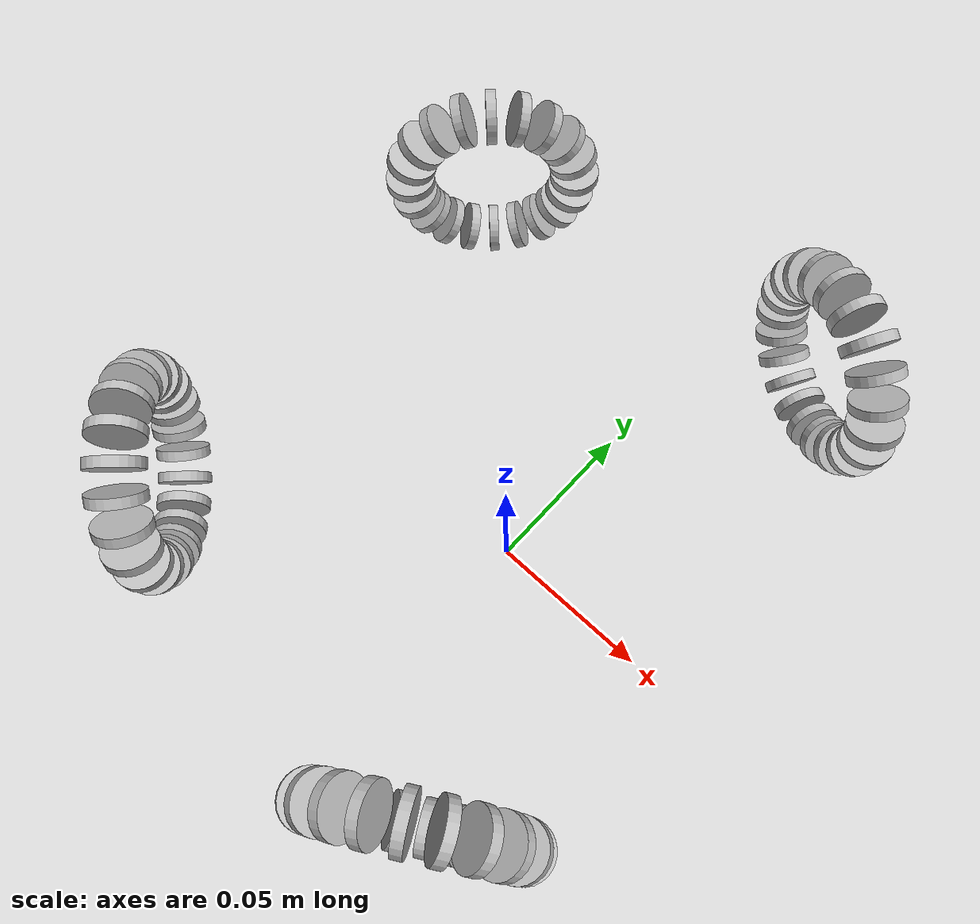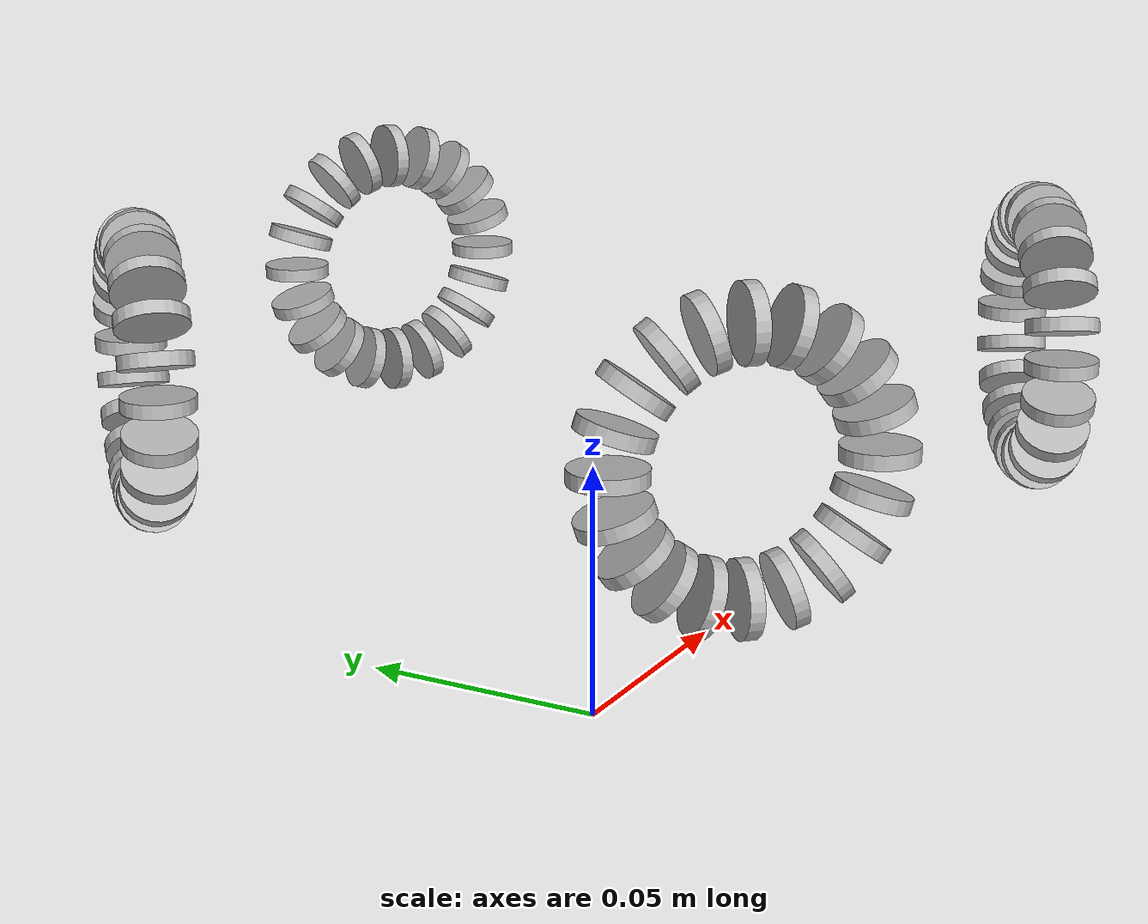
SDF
<sdf version='1.5'>
  <model name='ssl_robot'>
    <link name='base_link'>
      <pose frame=''>0 0 0 0 -0 0</pose>
      <inertial>
        <pose frame=''>0 0 0.09 0 -0 0</pose>
        <mass>2.5</mass>
        <inertia>
          <ixx>0.005812</ixx>
          <ixy>0</ixy>
          <ixz>0</ixz>
          <iyy>0.005812</iyy>
          <iyz>0</iyz>
          <izz>0.010125</izz>
        </inertia>
      </inertial>
      <collision name='base_link_lump::base_plate_collision'>
        <pose frame=''>0 0 0.0525 0 -0 0</pose>
        <geometry>
          <cylinder>
            <length>0.001</length>
            <radius>0.07</radius>
          </cylinder>
        </geometry>
      </collision>
      <gravity>1</gravity>
      <velocity_decay/>
      <self_collide>0</self_collide>
    </link>
    <link name='wheel_fl'>
      <pose frame=''>0.0375 0.06495 0.075 0 -0 1.0472</pose>
      <inertial>
        <pose frame=''>0.007 0 0 0 1.5707 0</pose>
        <mass>0.005</mass>
        <inertia>
          <ixx>8.229e-07</ixx>
          <ixy>0</ixy>
          <ixz>0</ixz>
          <iyy>8.229e-07</iyy>
          <iyz>0</iyz>
          <izz>1.5625e-06</izz>
        </inertia>
      </inertial>
      <gravity>1</gravity>
      <velocity_decay/>
      <self_collide>0</self_collide>
    </link>
    <joint name='base_wheel_fl' type='revolute'>
      <child>wheel_fl</child>
      <parent>base_link</parent>
      <axis>
        <xyz>0.499998 0.866027 0</xyz>
        <limit>
          <lower>-1e+16</lower>
          <upper>1e+16</upper>
        </limit>
        <dynamics>
          <spring_reference>0</spring_reference>
          <spring_stiffness>0</spring_stiffness>
        </dynamics>
        <use_parent_model_frame>1</use_parent_model_frame>
      </axis>
      <physics>
        <ode>
          <limit>
            <cfm>0</cfm>
            <erp>0.2</erp>
          </limit>
        </ode>
      </physics>
    </joint>
    <link name='sub_wheel_fl_1'>
      <pose frame=''>0.021947 0.082012 0.075 0 -0 1.0472</pose>
      <inertial>
        <pose frame=''>0 0 0 0 -0 0</pose>
        <mass>0.001</mass>
        <inertia>
          <ixx>1.11e-08</ixx>
          <ixy>0</ixy>
          <ixz>0</ixz>
          <iyy>1.11e-08</iyy>
          <iyz>0</iyz>
          <izz>2.11e-08</izz>
        </inertia>
      </inertial>
      <collision name='sub_wheel_fl_1_lump::wheel_collision'>
        <pose frame=''>0 0 0 0 -0 0</pose>
        <geometry>
          <cylinder>
            <length>0.0025</length>
            <radius>0.0065</radius>
          </cylinder>
        </geometry>
      </collision>
      <visual name='sub_wheel_fl_1_lump::wheel-visual_visual'>
        <pose frame=''>0 0 0 0 -0 0</pose>
        <geometry>
          <cylinder>
            <length>0.0025</length>
            <radius>0.0065</radius>
          </cylinder>
        </geometry>
      </visual>
      <gravity>1</gravity>
      <velocity_decay/>
      <self_collide>0</self_collide>
    </link>
    <joint name='wheel_subwheel_fl_1' type='revolute'>
      <child>sub_wheel_fl_1</child>
      <parent>wheel_fl</parent>
      <axis>
        <xyz>0 0 1</xyz>
        <limit>
          <lower>-1e+16</lower>
          <upper>1e+16</upper>
        </limit>
        <dynamics>
          <spring_reference>0</spring_reference>
          <spring_stiffness>0</spring_stiffness>
        </dynamics>
        <use_parent_model_frame>1</use_parent_model_frame>
      </axis>
    </joint>
    <link name='sub_wheel_fl_10'>
      <pose frame=''>0.05912 0.060551 0.081798 2.82743 0 1.0472</pose>
      <inertial>
        <pose frame=''>0 0 0 0 -0 0</pose>
        <mass>0.001</mass>
        <inertia>
          <ixx>1.11e-08</ixx>
          <ixy>0</ixy>
          <ixz>0</ixz>
          <iyy>1.11e-08</iyy>
          <iyz>0</iyz>
          <izz>2.11e-08</izz>
        </inertia>
      </inertial>
      <collision name='sub_wheel_fl_10_lump::wheel_collision'>
        <pose frame=''>0 0 0 0 -0 0</pose>
        <geometry>
          <cylinder>
            <length>0.0025</length>
            <radius>0.0065</radius>
          </cylinder>
        </geometry>
      </collision>
      <visual name='sub_wheel_fl_10_lump::wheel-visual_visual'>
        <pose frame=''>0 0 0 0 -0 0</pose>
        <geometry>
          <cylinder>
            <length>0.0025</length>
            <radius>0.0065</radius>
          </cylinder>
        </geometry>
      </visual>
      <gravity>1</gravity>
      <velocity_decay/>
      <self_collide>0</self_collide>
    </link>
    <joint name='wheel_subwheel_fl_10' type='revolute'>
      <child>sub_wheel_fl_10</child>
      <parent>wheel_fl</parent>
      <axis>
        <xyz>0.267617 -0.154508 -0.951056</xyz>
        <limit>
          <lower>-1e+16</lower>
          <upper>1e+16</upper>
        </limit>
        <dynamics>
          <spring_reference>0</spring_reference>
          <spring_stiffness>0</spring_stiffness>
        </dynamics>
        <use_parent_model_frame>1</use_parent_model_frame>
      </axis>
    </joint>
    <link name='sub_wheel_fl_11'>
      <pose frame=''>0.060053 0.060012 0.075 -3.14159 0 1.0472</pose>
      <inertial>
        <pose frame=''>0 0 0 0 -0 0</pose>
        <mass>0.001</mass>
        <inertia>
          <ixx>1.11e-08</ixx>
          <ixy>0</ixy>
          <ixz>0</ixz>
          <iyy>1.11e-08</iyy>
          <iyz>0</iyz>
          <izz>2.11e-08</izz>
        </inertia>
      </inertial>
      <collision name='sub_wheel_fl_11_lump::wheel_collision'>
        <pose frame=''>0 0 0 0 -0 0</pose>
        <geometry>
          <cylinder>
            <length>0.0025</length>
            <radius>0.0065</radius>
          </cylinder>
        </geometry>
      </collision>
      <visual name='sub_wheel_fl_11_lump::wheel-visual_visual'>
        <pose frame=''>0 0 0 0 -0 0</pose>
        <geometry>
          <cylinder>
            <length>0.0025</length>
            <radius>0.0065</radius>
          </cylinder>
        </geometry>
      </visual>
      <gravity>1</gravity>
      <velocity_decay/>
      <self_collide>0</self_collide>
    </link>
    <joint name='wheel_subwheel_fl_11' type='revolute'>
      <child>sub_wheel_fl_11</child>
      <parent>wheel_fl</parent>
      <axis>
        <xyz>-0 0 -1</xyz>
        <limit>
          <lower>-1e+16</lower>
          <upper>1e+16</upper>
        </limit>
        <dynamics>
          <spring_reference>0</spring_reference>
          <spring_stiffness>0</spring_stiffness>
        </dynamics>
        <use_parent_model_frame>1</use_parent_model_frame>
      </axis>
    </joint>
    <link name='sub_wheel_fl_12'>
      <pose frame=''>0.05912 0.060551 0.068202 -2.82743 -0 1.0472</pose>
      <inertial>
        <pose frame=''>0 0 0 0 -0 0</pose>
        <mass>0.001</mass>
        <inertia>
          <ixx>1.11e-08</ixx>
          <ixy>0</ixy>
          <ixz>0</ixz>
          <iyy>1.11e-08</iyy>
          <iyz>0</iyz>
          <izz>2.11e-08</izz>
        </inertia>
      </inertial>
      <collision name='sub_wheel_fl_12_lump::wheel_collision'>
        <pose frame=''>0 0 0 0 -0 0</pose>
        <geometry>
          <cylinder>
            <length>0.0025</length>
            <radius>0.0065</radius>
          </cylinder>
        </geometry>
      </collision>
      <visual name='sub_wheel_fl_12_lump::wheel-visual_visual'>
        <pose frame=''>0 0 0 0 -0 0</pose>
        <geometry>
          <cylinder>
            <length>0.0025</length>
            <radius>0.0065</radius>
          </cylinder>
        </geometry>
      </visual>
      <gravity>1</gravity>
      <velocity_decay/>
      <self_collide>0</self_collide>
    </link>
    <joint name='wheel_subwheel_fl_12' type='revolute'>
      <child>sub_wheel_fl_12</child>
      <parent>wheel_fl</parent>
      <axis>
        <xyz>-0.267617 0.154508 -0.951056</xyz>
        <limit>
          <lower>-1e+16</lower>
          <upper>1e+16</upper>
        </limit>
        <dynamics>
          <spring_reference>0</spring_reference>
          <spring_stiffness>0</spring_stiffness>
        </dynamics>
        <use_parent_model_frame>1</use_parent_model_frame>
      </axis>
    </joint>
    <link name='sub_wheel_fl_13'>
      <pose frame=''>0.056414 0.062113 0.062069 -2.51327 -0 1.0472</pose>
      <inertial>
        <pose frame=''>0 0 0 0 -0 0</pose>
        <mass>0.001</mass>
        <inertia>
          <ixx>1.11e-08</ixx>
          <ixy>0</ixy>
          <ixz>0</ixz>
          <iyy>1.11e-08</iyy>
          <iyz>0</iyz>
          <izz>2.11e-08</izz>
        </inertia>
      </inertial>
      <collision name='sub_wheel_fl_13_lump::wheel_collision'>
        <pose frame=''>0 0 0 0 -0 0</pose>
        <geometry>
          <cylinder>
            <length>0.0025</length>
            <radius>0.0065</radius>
          </cylinder>
        </geometry>
      </collision>
      <visual name='sub_wheel_fl_13_lump::wheel-visual_visual'>
        <pose frame=''>0 0 0 0 -0 0</pose>
        <geometry>
          <cylinder>
            <length>0.0025</length>
            <radius>0.0065</radius>
          </cylinder>
        </geometry>
      </visual>
      <gravity>1</gravity>
      <velocity_decay/>
      <self_collide>0</self_collide>
    </link>
    <joint name='wheel_subwheel_fl_13' type='revolute'>
      <child>sub_wheel_fl_13</child>
      <parent>wheel_fl</parent>
      <axis>
        <xyz>-0.509038 0.293891 -0.809017</xyz>
        <limit>
          <lower>-1e+16</lower>
          <upper>1e+16</upper>
        </limit>
        <dynamics>
          <spring_reference>0</spring_reference>
          <spring_stiffness>0</spring_stiffness>
        </dynamics>
        <use_parent_model_frame>1</use_parent_model_frame>
      </axis>
    </joint>
    <link name='sub_wheel_fl_14'>
      <pose frame=''>0.052199 0.064547 0.057202 -2.19912 -0 1.0472</pose>
      <inertial>
        <pose frame=''>0 0 0 0 -0 0</pose>
        <mass>0.001</mass>
        <inertia>
          <ixx>1.11e-08</ixx>
          <ixy>0</ixy>
          <ixz>0</ixz>
          <iyy>1.11e-08</iyy>
          <iyz>0</iyz>
          <izz>2.11e-08</izz>
        </inertia>
      </inertial>
      <collision name='sub_wheel_fl_14_lump::wheel_collision'>
        <pose frame=''>0 0 0 0 -0 0</pose>
        <geometry>
          <cylinder>
            <length>0.0025</length>
            <radius>0.0065</radius>
          </cylinder>
        </geometry>
      </collision>
      <visual name='sub_wheel_fl_14_lump::wheel-visual_visual'>
        <pose frame=''>0 0 0 0 -0 0</pose>
        <geometry>
          <cylinder>
            <length>0.0025</length>
            <radius>0.0065</radius>
          </cylinder>
        </geometry>
      </visual>
      <gravity>1</gravity>
      <velocity_decay/>
      <self_collide>0</self_collide>
    </link>
    <joint name='wheel_subwheel_fl_14' type='revolute'>
      <child>sub_wheel_fl_14</child>
      <parent>wheel_fl</parent>
      <axis>
        <xyz>-0.70063 0.404507 -0.587786</xyz>
        <limit>
          <lower>-1e+16</lower>
          <upper>1e+16</upper>
        </limit>
        <dynamics>
          <spring_reference>0</spring_reference>
          <spring_stiffness>0</spring_stiffness>
        </dynamics>
        <use_parent_model_frame>1</use_parent_model_frame>
      </axis>
    </joint>
    <link name='sub_wheel_fl_15'>
      <pose frame=''>0.046888 0.067613 0.054077 -1.88496 -0 1.0472</pose>
      <inertial>
        <pose frame=''>0 0 0 0 -0 0</pose>
        <mass>0.001</mass>
        <inertia>
          <ixx>1.11e-08</ixx>
          <ixy>0</ixy>
          <ixz>0</ixz>
          <iyy>1.11e-08</iyy>
          <iyz>0</iyz>
          <izz>2.11e-08</izz>
        </inertia>
      </inertial>
      <collision name='sub_wheel_fl_15_lump::wheel_collision'>
        <pose frame=''>0 0 0 0 -0 0</pose>
        <geometry>
          <cylinder>
            <length>0.0025</length>
            <radius>0.0065</radius>
          </cylinder>
        </geometry>
      </collision>
      <visual name='sub_wheel_fl_15_lump::wheel-visual_visual'>
        <pose frame=''>0 0 0 0 -0 0</pose>
        <geometry>
          <cylinder>
            <length>0.0025</length>
            <radius>0.0065</radius>
          </cylinder>
        </geometry>
      </visual>
      <gravity>1</gravity>
      <velocity_decay/>
      <self_collide>0</self_collide>
    </link>
    <joint name='wheel_subwheel_fl_15' type='revolute'>
      <child>sub_wheel_fl_15</child>
      <parent>wheel_fl</parent>
      <axis>
        <xyz>-0.82364 0.475526 -0.309017</xyz>
        <limit>
          <lower>-1e+16</lower>
          <upper>1e+16</upper>
        </limit>
        <dynamics>
          <spring_reference>0</spring_reference>
          <spring_stiffness>0</spring_stiffness>
        </dynamics>
        <use_parent_model_frame>1</use_parent_model_frame>
      </axis>
    </joint>
    <link name='sub_wheel_fl_16'>
      <pose frame=''>0.041 0.071012 0.053 -1.5708 -0 1.0472</pose>
      <inertial>
        <pose frame=''>0 0 0 0 -0 0</pose>
        <mass>0.001</mass>
        <inertia>
          <ixx>1.11e-08</ixx>
          <ixy>0</ixy>
          <ixz>0</ixz>
          <iyy>1.11e-08</iyy>
          <iyz>0</iyz>
          <izz>2.11e-08</izz>
        </inertia>
      </inertial>
      <collision name='sub_wheel_fl_16_lump::wheel_collision'>
        <pose frame=''>0 0 0 0 -0 0</pose>
        <geometry>
          <cylinder>
            <length>0.0025</length>
            <radius>0.0065</radius>
          </cylinder>
        </geometry>
      </collision>
      <visual name='sub_wheel_fl_16_lump::wheel-visual_visual'>
        <pose frame=''>0 0 0 0 -0 0</pose>
        <geometry>
          <cylinder>
            <length>0.0025</length>
            <radius>0.0065</radius>
          </cylinder>
        </geometry>
      </visual>
      <gravity>1</gravity>
      <velocity_decay/>
      <self_collide>0</self_collide>
    </link>
    <joint name='wheel_subwheel_fl_16' type='revolute'>
      <child>sub_wheel_fl_16</child>
      <parent>wheel_fl</parent>
      <axis>
        <xyz>-0.866027 0.499998 0</xyz>
        <limit>
          <lower>-1e+16</lower>
          <upper>1e+16</upper>
        </limit>
        <dynamics>
          <spring_reference>0</spring_reference>
          <spring_stiffness>0</spring_stiffness>
        </dynamics>
        <use_parent_model_frame>1</use_parent_model_frame>
      </axis>
    </joint>
    <link name='sub_wheel_fl_17'>
      <pose frame=''>0.035112 0.074411 0.054077 -1.25664 -0 1.0472</pose>
      <inertial>
        <pose frame=''>0 0 0 0 -0 0</pose>
        <mass>0.001</mass>
        <inertia>
          <ixx>1.11e-08</ixx>
          <ixy>0</ixy>
          <ixz>0</ixz>
          <iyy>1.11e-08</iyy>
          <iyz>0</iyz>
          <izz>2.11e-08</izz>
        </inertia>
      </inertial>
      <collision name='sub_wheel_fl_17_lump::wheel_collision'>
        <pose frame=''>0 0 0 0 -0 0</pose>
        <geometry>
          <cylinder>
            <length>0.0025</length>
            <radius>0.0065</radius>
          </cylinder>
        </geometry>
      </collision>
      <visual name='sub_wheel_fl_17_lump::wheel-visual_visual'>
        <pose frame=''>0 0 0 0 -0 0</pose>
        <geometry>
          <cylinder>
            <length>0.0025</length>
            <radius>0.0065</radius>
          </cylinder>
        </geometry>
      </visual>
      <gravity>1</gravity>
      <velocity_decay/>
      <self_collide>0</self_collide>
    </link>
    <joint name='wheel_subwheel_fl_17' type='revolute'>
      <child>sub_wheel_fl_17</child>
      <parent>wheel_fl</parent>
      <axis>
        <xyz>-0.82364 0.475526 0.309017</xyz>
        <limit>
          <lower>-1e+16</lower>
          <upper>1e+16</upper>
        </limit>
        <dynamics>
          <spring_reference>0</spring_reference>
          <spring_stiffness>0</spring_stiffness>
        </dynamics>
        <use_parent_model_frame>1</use_parent_model_frame>
      </axis>
    </joint>
    <link name='sub_wheel_fl_18'>
      <pose frame=''>0.029801 0.077478 0.057202 -0.942477 -0 1.0472</pose>
      <inertial>
        <pose frame=''>0 0 0 0 -0 0</pose>
        <mass>0.001</mass>
        <inertia>
          <ixx>1.11e-08</ixx>
          <ixy>0</ixy>
          <ixz>0</ixz>
          <iyy>1.11e-08</iyy>
          <iyz>0</iyz>
          <izz>2.11e-08</izz>
        </inertia>
      </inertial>
      <collision name='sub_wheel_fl_18_lump::wheel_collision'>
        <pose frame=''>0 0 0 0 -0 0</pose>
        <geometry>
          <cylinder>
            <length>0.0025</length>
            <radius>0.0065</radius>
          </cylinder>
        </geometry>
      </collision>
      <visual name='sub_wheel_fl_18_lump::wheel-visual_visual'>
        <pose frame=''>0 0 0 0 -0 0</pose>
        <geometry>
          <cylinder>
            <length>0.0025</length>
            <radius>0.0065</radius>
          </cylinder>
        </geometry>
      </visual>
      <gravity>1</gravity>
      <velocity_decay/>
      <self_collide>0</self_collide>
    </link>
    <joint name='wheel_subwheel_fl_18' type='revolute'>
      <child>sub_wheel_fl_18</child>
      <parent>wheel_fl</parent>
      <axis>
        <xyz>-0.70063 0.404507 0.587786</xyz>
        <limit>
          <lower>-1e+16</lower>
          <upper>1e+16</upper>
        </limit>
        <dynamics>
          <spring_reference>0</spring_reference>
          <spring_stiffness>0</spring_stiffness>
        </dynamics>
        <use_parent_model_frame>1</use_parent_model_frame>
      </axis>
    </joint>
    <link name='sub_wheel_fl_19'>
      <pose frame=''>0.025586 0.079911 0.062069 -0.628318 -0 1.0472</pose>
      <inertial>
        <pose frame=''>0 0 0 0 -0 0</pose>
        <mass>0.001</mass>
        <inertia>
          <ixx>1.11e-08</ixx>
          <ixy>0</ixy>
          <ixz>0</ixz>
          <iyy>1.11e-08</iyy>
          <iyz>0</iyz>
          <izz>2.11e-08</izz>
        </inertia>
      </inertial>
      <collision name='sub_wheel_fl_19_lump::wheel_collision'>
        <pose frame=''>0 0 0 0 -0 0</pose>
        <geometry>
          <cylinder>
            <length>0.0025</length>
            <radius>0.0065</radius>
          </cylinder>
        </geometry>
      </collision>
      <visual name='sub_wheel_fl_19_lump::wheel-visual_visual'>
        <pose frame=''>0 0 0 0 -0 0</pose>
        <geometry>
          <cylinder>
            <length>0.0025</length>
            <radius>0.0065</radius>
          </cylinder>
        </geometry>
      </visual>
      <gravity>1</gravity>
      <velocity_decay/>
      <self_collide>0</self_collide>
    </link>
    <joint name='wheel_subwheel_fl_19' type='revolute'>
      <child>sub_wheel_fl_19</child>
      <parent>wheel_fl</parent>
      <axis>
        <xyz>-0.509038 0.293891 0.809017</xyz>
        <limit>
          <lower>-1e+16</lower>
          <upper>1e+16</upper>
        </limit>
        <dynamics>
          <spring_reference>0</spring_reference>
          <spring_stiffness>0</spring_stiffness>
        </dynamics>
        <use_parent_model_frame>1</use_parent_model_frame>
      </axis>
    </joint>
    <link name='sub_wheel_fl_2'>
      <pose frame=''>0.02288 0.081474 0.081798 0.314159 -0 1.0472</pose>
      <inertial>
        <pose frame=''>0 0 0 0 -0 0</pose>
        <mass>0.001</mass>
        <inertia>
          <ixx>1.11e-08</ixx>
          <ixy>0</ixy>
          <ixz>0</ixz>
          <iyy>1.11e-08</iyy>
          <iyz>0</iyz>
          <izz>2.11e-08</izz>
        </inertia>
      </inertial>
      <collision name='sub_wheel_fl_2_lump::wheel_collision'>
        <pose frame=''>0 0 0 0 -0 0</pose>
        <geometry>
          <cylinder>
            <length>0.0025</length>
            <radius>0.0065</radius>
          </cylinder>
        </geometry>
      </collision>
      <visual name='sub_wheel_fl_2_lump::wheel-visual_visual'>
        <pose frame=''>0 0 0 0 -0 0</pose>
        <geometry>
          <cylinder>
            <length>0.0025</length>
            <radius>0.0065</radius>
          </cylinder>
        </geometry>
      </visual>
      <gravity>1</gravity>
      <velocity_decay/>
      <self_collide>0</self_collide>
    </link>
    <joint name='wheel_subwheel_fl_2' type='revolute'>
      <child>sub_wheel_fl_2</child>
      <parent>wheel_fl</parent>
      <axis>
        <xyz>0.267617 -0.154508 0.951057</xyz>
        <limit>
          <lower>-1e+16</lower>
          <upper>1e+16</upper>
        </limit>
        <dynamics>
          <spring_reference>0</spring_reference>
          <spring_stiffness>0</spring_stiffness>
        </dynamics>
        <use_parent_model_frame>1</use_parent_model_frame>
      </axis>
    </joint>
    <link name='sub_wheel_fl_20'>
      <pose frame=''>0.02288 0.081474 0.068202 -0.314159 0 1.0472</pose>
      <inertial>
        <pose frame=''>0 0 0 0 -0 0</pose>
        <mass>0.001</mass>
        <inertia>
          <ixx>1.11e-08</ixx>
          <ixy>0</ixy>
          <ixz>0</ixz>
          <iyy>1.11e-08</iyy>
          <iyz>0</iyz>
          <izz>2.11e-08</izz>
        </inertia>
      </inertial>
      <collision name='sub_wheel_fl_20_lump::wheel_collision'>
        <pose frame=''>0 0 0 0 -0 0</pose>
        <geometry>
          <cylinder>
            <length>0.0025</length>
            <radius>0.0065</radius>
          </cylinder>
        </geometry>
      </collision>
      <visual name='sub_wheel_fl_20_lump::wheel-visual_visual'>
        <pose frame=''>0 0 0 0 -0 0</pose>
        <geometry>
          <cylinder>
            <length>0.0025</length>
            <radius>0.0065</radius>
          </cylinder>
        </geometry>
      </visual>
      <gravity>1</gravity>
      <velocity_decay/>
      <self_collide>0</self_collide>
    </link>
    <joint name='wheel_subwheel_fl_20' type='revolute'>
      <child>sub_wheel_fl_20</child>
      <parent>wheel_fl</parent>
      <axis>
        <xyz>-0.267617 0.154508 0.951057</xyz>
        <limit>
          <lower>-1e+16</lower>
          <upper>1e+16</upper>
        </limit>
        <dynamics>
          <spring_reference>0</spring_reference>
          <spring_stiffness>0</spring_stiffness>
        </dynamics>
        <use_parent_model_frame>1</use_parent_model_frame>
      </axis>
    </joint>
    <link name='sub_wheel_fl_3'>
      <pose frame=''>0.025586 0.079911 0.087931 0.628319 -0 1.0472</pose>
      <inertial>
        <pose frame=''>0 0 0 0 -0 0</pose>
        <mass>0.001</mass>
        <inertia>
          <ixx>1.11e-08</ixx>
          <ixy>0</ixy>
          <ixz>0</ixz>
          <iyy>1.11e-08</iyy>
          <iyz>0</iyz>
          <izz>2.11e-08</izz>
        </inertia>
      </inertial>
      <collision name='sub_wheel_fl_3_lump::wheel_collision'>
        <pose frame=''>0 0 0 0 -0 0</pose>
        <geometry>
          <cylinder>
            <length>0.0025</length>
            <radius>0.0065</radius>
          </cylinder>
        </geometry>
      </collision>
      <visual name='sub_wheel_fl_3_lump::wheel-visual_visual'>
        <pose frame=''>0 0 0 0 -0 0</pose>
        <geometry>
          <cylinder>
            <length>0.0025</length>
            <radius>0.0065</radius>
          </cylinder>
        </geometry>
      </visual>
      <gravity>1</gravity>
      <velocity_decay/>
      <self_collide>0</self_collide>
    </link>
    <joint name='wheel_subwheel_fl_3' type='revolute'>
      <child>sub_wheel_fl_3</child>
      <parent>wheel_fl</parent>
      <axis>
        <xyz>0.509038 -0.293892 0.809017</xyz>
        <limit>
          <lower>-1e+16</lower>
          <upper>1e+16</upper>
        </limit>
        <dynamics>
          <spring_reference>0</spring_reference>
          <spring_stiffness>0</spring_stiffness>
        </dynamics>
        <use_parent_model_frame>1</use_parent_model_frame>
      </axis>
    </joint>
    <link name='sub_wheel_fl_4'>
      <pose frame=''>0.029801 0.077478 0.092798 0.942478 -0 1.0472</pose>
      <inertial>
        <pose frame=''>0 0 0 0 -0 0</pose>
        <mass>0.001</mass>
        <inertia>
          <ixx>1.11e-08</ixx>
          <ixy>0</ixy>
          <ixz>0</ixz>
          <iyy>1.11e-08</iyy>
          <iyz>0</iyz>
          <izz>2.11e-08</izz>
        </inertia>
      </inertial>
      <collision name='sub_wheel_fl_4_lump::wheel_collision'>
        <pose frame=''>0 0 0 0 -0 0</pose>
        <geometry>
          <cylinder>
            <length>0.0025</length>
            <radius>0.0065</radius>
          </cylinder>
        </geometry>
      </collision>
      <visual name='sub_wheel_fl_4_lump::wheel-visual_visual'>
        <pose frame=''>0 0 0 0 -0 0</pose>
        <geometry>
          <cylinder>
            <length>0.0025</length>
            <radius>0.0065</radius>
          </cylinder>
        </geometry>
      </visual>
      <gravity>1</gravity>
      <velocity_decay/>
      <self_collide>0</self_collide>
    </link>
    <joint name='wheel_subwheel_fl_4' type='revolute'>
      <child>sub_wheel_fl_4</child>
      <parent>wheel_fl</parent>
      <axis>
        <xyz>0.70063 -0.404507 0.587785</xyz>
        <limit>
          <lower>-1e+16</lower>
          <upper>1e+16</upper>
        </limit>
        <dynamics>
          <spring_reference>0</spring_reference>
          <spring_stiffness>0</spring_stiffness>
        </dynamics>
        <use_parent_model_frame>1</use_parent_model_frame>
      </axis>
    </joint>
    <link name='sub_wheel_fl_5'>
      <pose frame=''>0.035112 0.074411 0.095923 1.25664 0 1.0472</pose>
      <inertial>
        <pose frame=''>0 0 0 0 -0 0</pose>
        <mass>0.001</mass>
        <inertia>
          <ixx>1.11e-08</ixx>
          <ixy>0</ixy>
          <ixz>0</ixz>
          <iyy>1.11e-08</iyy>
          <iyz>0</iyz>
          <izz>2.11e-08</izz>
        </inertia>
      </inertial>
      <collision name='sub_wheel_fl_5_lump::wheel_collision'>
        <pose frame=''>0 0 0 0 -0 0</pose>
        <geometry>
          <cylinder>
            <length>0.0025</length>
            <radius>0.0065</radius>
          </cylinder>
        </geometry>
      </collision>
      <visual name='sub_wheel_fl_5_lump::wheel-visual_visual'>
        <pose frame=''>0 0 0 0 -0 0</pose>
        <geometry>
          <cylinder>
            <length>0.0025</length>
            <radius>0.0065</radius>
          </cylinder>
        </geometry>
      </visual>
      <gravity>1</gravity>
      <velocity_decay/>
      <self_collide>0</self_collide>
    </link>
    <joint name='wheel_subwheel_fl_5' type='revolute'>
      <child>sub_wheel_fl_5</child>
      <parent>wheel_fl</parent>
      <axis>
        <xyz>0.82364 -0.475526 0.309017</xyz>
        <limit>
          <lower>-1e+16</lower>
          <upper>1e+16</upper>
        </limit>
        <dynamics>
          <spring_reference>0</spring_reference>
          <spring_stiffness>0</spring_stiffness>
        </dynamics>
        <use_parent_model_frame>1</use_parent_model_frame>
      </axis>
    </joint>
    <link name='sub_wheel_fl_6'>
      <pose frame=''>0.041 0.071012 0.097 1.5708 -0 1.0472</pose>
      <inertial>
        <pose frame=''>0 0 0 0 -0 0</pose>
        <mass>0.001</mass>
        <inertia>
          <ixx>1.11e-08</ixx>
          <ixy>0</ixy>
          <ixz>0</ixz>
          <iyy>1.11e-08</iyy>
          <iyz>0</iyz>
          <izz>2.11e-08</izz>
        </inertia>
      </inertial>
      <collision name='sub_wheel_fl_6_lump::wheel_collision'>
        <pose frame=''>0 0 0 0 -0 0</pose>
        <geometry>
          <cylinder>
            <length>0.0025</length>
            <radius>0.0065</radius>
          </cylinder>
        </geometry>
      </collision>
      <visual name='sub_wheel_fl_6_lump::wheel-visual_visual'>
        <pose frame=''>0 0 0 0 -0 0</pose>
        <geometry>
          <cylinder>
            <length>0.0025</length>
            <radius>0.0065</radius>
          </cylinder>
        </geometry>
      </visual>
      <gravity>1</gravity>
      <velocity_decay/>
      <self_collide>0</self_collide>
    </link>
    <joint name='wheel_subwheel_fl_6' type='revolute'>
      <child>sub_wheel_fl_6</child>
      <parent>wheel_fl</parent>
      <axis>
        <xyz>0.866027 -0.499998 0</xyz>
        <limit>
          <lower>-1e+16</lower>
          <upper>1e+16</upper>
        </limit>
        <dynamics>
          <spring_reference>0</spring_reference>
          <spring_stiffness>0</spring_stiffness>
        </dynamics>
        <use_parent_model_frame>1</use_parent_model_frame>
      </axis>
    </joint>
    <link name='sub_wheel_fl_7'>
      <pose frame=''>0.046888 0.067613 0.095923 1.88496 -0 1.0472</pose>
      <inertial>
        <pose frame=''>0 0 0 0 -0 0</pose>
        <mass>0.001</mass>
        <inertia>
          <ixx>1.11e-08</ixx>
          <ixy>0</ixy>
          <ixz>0</ixz>
          <iyy>1.11e-08</iyy>
          <iyz>0</iyz>
          <izz>2.11e-08</izz>
        </inertia>
      </inertial>
      <collision name='sub_wheel_fl_7_lump::wheel_collision'>
        <pose frame=''>0 0 0 0 -0 0</pose>
        <geometry>
          <cylinder>
            <length>0.0025</length>
            <radius>0.0065</radius>
          </cylinder>
        </geometry>
      </collision>
      <visual name='sub_wheel_fl_7_lump::wheel-visual_visual'>
        <pose frame=''>0 0 0 0 -0 0</pose>
        <geometry>
          <cylinder>
            <length>0.0025</length>
            <radius>0.0065</radius>
          </cylinder>
        </geometry>
      </visual>
      <gravity>1</gravity>
      <velocity_decay/>
      <self_collide>0</self_collide>
    </link>
    <joint name='wheel_subwheel_fl_7' type='revolute'>
      <child>sub_wheel_fl_7</child>
      <parent>wheel_fl</parent>
      <axis>
        <xyz>0.82364 -0.475526 -0.309017</xyz>
        <limit>
          <lower>-1e+16</lower>
          <upper>1e+16</upper>
        </limit>
        <dynamics>
          <spring_reference>0</spring_reference>
          <spring_stiffness>0</spring_stiffness>
        </dynamics>
        <use_parent_model_frame>1</use_parent_model_frame>
      </axis>
    </joint>
    <link name='sub_wheel_fl_8'>
      <pose frame=''>0.052199 0.064547 0.092798 2.19911 -0 1.0472</pose>
      <inertial>
        <pose frame=''>0 0 0 0 -0 0</pose>
        <mass>0.001</mass>
        <inertia>
          <ixx>1.11e-08</ixx>
          <ixy>0</ixy>
          <ixz>0</ixz>
          <iyy>1.11e-08</iyy>
          <iyz>0</iyz>
          <izz>2.11e-08</izz>
        </inertia>
      </inertial>
      <collision name='sub_wheel_fl_8_lump::wheel_collision'>
        <pose frame=''>0 0 0 0 -0 0</pose>
        <geometry>
          <cylinder>
            <length>0.0025</length>
            <radius>0.0065</radius>
          </cylinder>
        </geometry>
      </collision>
      <visual name='sub_wheel_fl_8_lump::wheel-visual_visual'>
        <pose frame=''>0 0 0 0 -0 0</pose>
        <geometry>
          <cylinder>
            <length>0.0025</length>
            <radius>0.0065</radius>
          </cylinder>
        </geometry>
      </visual>
      <gravity>1</gravity>
      <velocity_decay/>
      <self_collide>0</self_collide>
    </link>
    <joint name='wheel_subwheel_fl_8' type='revolute'>
      <child>sub_wheel_fl_8</child>
      <parent>wheel_fl</parent>
      <axis>
        <xyz>0.70063 -0.404507 -0.587785</xyz>
        <limit>
          <lower>-1e+16</lower>
          <upper>1e+16</upper>
        </limit>
        <dynamics>
          <spring_reference>0</spring_reference>
          <spring_stiffness>0</spring_stiffness>
        </dynamics>
        <use_parent_model_frame>1</use_parent_model_frame>
      </axis>
    </joint>
    <link name='sub_wheel_fl_9'>
      <pose frame=''>0.056414 0.062113 0.087931 2.51327 0 1.0472</pose>
      <inertial>
        <pose frame=''>0 0 0 0 -0 0</pose>
        <mass>0.001</mass>
        <inertia>
          <ixx>1.11e-08</ixx>
          <ixy>0</ixy>
          <ixz>0</ixz>
          <iyy>1.11e-08</iyy>
          <iyz>0</iyz>
          <izz>2.11e-08</izz>
        </inertia>
      </inertial>
      <collision name='sub_wheel_fl_9_lump::wheel_collision'>
        <pose frame=''>0 0 0 0 -0 0</pose>
        <geometry>
          <cylinder>
            <length>0.0025</length>
            <radius>0.0065</radius>
          </cylinder>
        </geometry>
      </collision>
      <visual name='sub_wheel_fl_9_lump::wheel-visual_visual'>
        <pose frame=''>0 0 0 0 -0 0</pose>
        <geometry>
          <cylinder>
            <length>0.0025</length>
            <radius>0.0065</radius>
          </cylinder>
        </geometry>
      </visual>
      <gravity>1</gravity>
      <velocity_decay/>
      <self_collide>0</self_collide>
    </link>
    <joint name='wheel_subwheel_fl_9' type='revolute'>
      <child>sub_wheel_fl_9</child>
      <parent>wheel_fl</parent>
      <axis>
        <xyz>0.509038 -0.293891 -0.809017</xyz>
        <limit>
          <lower>-1e+16</lower>
          <upper>1e+16</upper>
        </limit>
        <dynamics>
          <spring_reference>0</spring_reference>
          <spring_stiffness>0</spring_stiffness>
        </dynamics>
        <use_parent_model_frame>1</use_parent_model_frame>
      </axis>
    </joint>
    <link name='wheel_fr'>
      <pose frame=''>0.0375 -0.06495 0.075 0 0 -1.0472</pose>
      <inertial>
        <pose frame=''>0.007 0 0 0 1.5707 0</pose>
        <mass>0.005</mass>
        <inertia>
          <ixx>8.229e-07</ixx>
          <ixy>0</ixy>
          <ixz>0</ixz>
          <iyy>8.229e-07</iyy>
          <iyz>0</iyz>
          <izz>1.5625e-06</izz>
        </inertia>
      </inertial>
      <gravity>1</gravity>
      <velocity_decay/>
      <self_collide>0</self_collide>
    </link>
    <joint name='base_wheel_fr' type='revolute'>
      <child>wheel_fr</child>
      <parent>base_link</parent>
      <axis>
        <xyz>0.499998 -0.866027 0</xyz>
        <limit>
          <lower>-1e+16</lower>
          <upper>1e+16</upper>
        </limit>
        <dynamics>
          <spring_reference>0</spring_reference>
          <spring_stiffness>0</spring_stiffness>
        </dynamics>
        <use_parent_model_frame>1</use_parent_model_frame>
      </axis>
      <physics>
        <ode>
          <limit>
            <cfm>0</cfm>
            <erp>0.2</erp>
          </limit>
        </ode>
      </physics>
    </joint>
    <link name='sub_wheel_fr_1'>
      <pose frame=''>0.060053 -0.060012 0.075 0 0 -1.0472</pose>
      <inertial>
        <pose frame=''>0 0 0 0 -0 0</pose>
        <mass>0.001</mass>
        <inertia>
          <ixx>1.11e-08</ixx>
          <ixy>0</ixy>
          <ixz>0</ixz>
          <iyy>1.11e-08</iyy>
          <iyz>0</iyz>
          <izz>2.11e-08</izz>
        </inertia>
      </inertial>
      <collision name='sub_wheel_fr_1_lump::wheel_collision'>
        <pose frame=''>0 0 0 0 -0 0</pose>
        <geometry>
          <cylinder>
            <length>0.0025</length>
            <radius>0.0065</radius>
          </cylinder>
        </geometry>
      </collision>
      <visual name='sub_wheel_fr_1_lump::wheel-visual_visual'>
        <pose frame=''>0 0 0 0 -0 0</pose>
        <geometry>
          <cylinder>
            <length>0.0025</length>
            <radius>0.0065</radius>
          </cylinder>
        </geometry>
      </visual>
      <gravity>1</gravity>
      <velocity_decay/>
      <self_collide>0</self_collide>
    </link>
    <joint name='wheel_subwheel_fr_1' type='revolute'>
      <child>sub_wheel_fr_1</child>
      <parent>wheel_fr</parent>
      <axis>
        <xyz>0 0 1</xyz>
        <limit>
          <lower>-1e+16</lower>
          <upper>1e+16</upper>
        </limit>
        <dynamics>
          <spring_reference>0</spring_reference>
          <spring_stiffness>0</spring_stiffness>
        </dynamics>
        <use_parent_model_frame>1</use_parent_model_frame>
      </axis>
    </joint>
    <link name='sub_wheel_fr_10'>
      <pose frame=''>0.02288 -0.081474 0.081798 2.82743 -0 -1.0472</pose>
      <inertial>
        <pose frame=''>0 0 0 0 -0 0</pose>
        <mass>0.001</mass>
        <inertia>
          <ixx>1.11e-08</ixx>
          <ixy>0</ixy>
          <ixz>0</ixz>
          <iyy>1.11e-08</iyy>
          <iyz>0</iyz>
          <izz>2.11e-08</izz>
        </inertia>
      </inertial>
      <collision name='sub_wheel_fr_10_lump::wheel_collision'>
        <pose frame=''>0 0 0 0 -0 0</pose>
        <geometry>
          <cylinder>
            <length>0.0025</length>
            <radius>0.0065</radius>
          </cylinder>
        </geometry>
      </collision>
      <visual name='sub_wheel_fr_10_lump::wheel-visual_visual'>
        <pose frame=''>0 0 0 0 -0 0</pose>
        <geometry>
          <cylinder>
            <length>0.0025</length>
            <radius>0.0065</radius>
          </cylinder>
        </geometry>
      </visual>
      <gravity>1</gravity>
      <velocity_decay/>
      <self_collide>0</self_collide>
    </link>
    <joint name='wheel_subwheel_fr_10' type='revolute'>
      <child>sub_wheel_fr_10</child>
      <parent>wheel_fr</parent>
      <axis>
        <xyz>-0.267617 -0.154508 -0.951056</xyz>
        <limit>
          <lower>-1e+16</lower>
          <upper>1e+16</upper>
        </limit>
        <dynamics>
          <spring_reference>0</spring_reference>
          <spring_stiffness>0</spring_stiffness>
        </dynamics>
        <use_parent_model_frame>1</use_parent_model_frame>
      </axis>
    </joint>
    <link name='sub_wheel_fr_11'>
      <pose frame=''>0.021947 -0.082012 0.075 -3.14159 -0 -1.0472</pose>
      <inertial>
        <pose frame=''>0 0 0 0 -0 0</pose>
        <mass>0.001</mass>
        <inertia>
          <ixx>1.11e-08</ixx>
          <ixy>0</ixy>
          <ixz>0</ixz>
          <iyy>1.11e-08</iyy>
          <iyz>0</iyz>
          <izz>2.11e-08</izz>
        </inertia>
      </inertial>
      <collision name='sub_wheel_fr_11_lump::wheel_collision'>
        <pose frame=''>0 0 0 0 -0 0</pose>
        <geometry>
          <cylinder>
            <length>0.0025</length>
            <radius>0.0065</radius>
          </cylinder>
        </geometry>
      </collision>
      <visual name='sub_wheel_fr_11_lump::wheel-visual_visual'>
        <pose frame=''>0 0 0 0 -0 0</pose>
        <geometry>
          <cylinder>
            <length>0.0025</length>
            <radius>0.0065</radius>
          </cylinder>
        </geometry>
      </visual>
      <gravity>1</gravity>
      <velocity_decay/>
      <self_collide>0</self_collide>
    </link>
    <joint name='wheel_subwheel_fr_11' type='revolute'>
      <child>sub_wheel_fr_11</child>
      <parent>wheel_fr</parent>
      <axis>
        <xyz>0 0 -1</xyz>
        <limit>
          <lower>-1e+16</lower>
          <upper>1e+16</upper>
        </limit>
        <dynamics>
          <spring_reference>0</spring_reference>
          <spring_stiffness>0</spring_stiffness>
        </dynamics>
        <use_parent_model_frame>1</use_parent_model_frame>
      </axis>
    </joint>
    <link name='sub_wheel_fr_12'>
      <pose frame=''>0.02288 -0.081474 0.068202 -2.82743 -0 -1.0472</pose>
      <inertial>
        <pose frame=''>0 0 0 0 -0 0</pose>
        <mass>0.001</mass>
        <inertia>
          <ixx>1.11e-08</ixx>
          <ixy>0</ixy>
          <ixz>0</ixz>
          <iyy>1.11e-08</iyy>
          <iyz>0</iyz>
          <izz>2.11e-08</izz>
        </inertia>
      </inertial>
      <collision name='sub_wheel_fr_12_lump::wheel_collision'>
        <pose frame=''>0 0 0 0 -0 0</pose>
        <geometry>
          <cylinder>
            <length>0.0025</length>
            <radius>0.0065</radius>
          </cylinder>
        </geometry>
      </collision>
      <visual name='sub_wheel_fr_12_lump::wheel-visual_visual'>
        <pose frame=''>0 0 0 0 -0 0</pose>
        <geometry>
          <cylinder>
            <length>0.0025</length>
            <radius>0.0065</radius>
          </cylinder>
        </geometry>
      </visual>
      <gravity>1</gravity>
      <velocity_decay/>
      <self_collide>0</self_collide>
    </link>
    <joint name='wheel_subwheel_fr_12' type='revolute'>
      <child>sub_wheel_fr_12</child>
      <parent>wheel_fr</parent>
      <axis>
        <xyz>0.267617 0.154508 -0.951056</xyz>
        <limit>
          <lower>-1e+16</lower>
          <upper>1e+16</upper>
        </limit>
        <dynamics>
          <spring_reference>0</spring_reference>
          <spring_stiffness>0</spring_stiffness>
        </dynamics>
        <use_parent_model_frame>1</use_parent_model_frame>
      </axis>
    </joint>
    <link name='sub_wheel_fr_13'>
      <pose frame=''>0.025586 -0.079911 0.062069 -2.51327 -0 -1.0472</pose>
      <inertial>
        <pose frame=''>0 0 0 0 -0 0</pose>
        <mass>0.001</mass>
        <inertia>
          <ixx>1.11e-08</ixx>
          <ixy>0</ixy>
          <ixz>0</ixz>
          <iyy>1.11e-08</iyy>
          <iyz>0</iyz>
          <izz>2.11e-08</izz>
        </inertia>
      </inertial>
      <collision name='sub_wheel_fr_13_lump::wheel_collision'>
        <pose frame=''>0 0 0 0 -0 0</pose>
        <geometry>
          <cylinder>
            <length>0.0025</length>
            <radius>0.0065</radius>
          </cylinder>
        </geometry>
      </collision>
      <visual name='sub_wheel_fr_13_lump::wheel-visual_visual'>
        <pose frame=''>0 0 0 0 -0 0</pose>
        <geometry>
          <cylinder>
            <length>0.0025</length>
            <radius>0.0065</radius>
          </cylinder>
        </geometry>
      </visual>
      <gravity>1</gravity>
      <velocity_decay/>
      <self_collide>0</self_collide>
    </link>
    <joint name='wheel_subwheel_fr_13' type='revolute'>
      <child>sub_wheel_fr_13</child>
      <parent>wheel_fr</parent>
      <axis>
        <xyz>0.509038 0.293891 -0.809017</xyz>
        <limit>
          <lower>-1e+16</lower>
          <upper>1e+16</upper>
        </limit>
        <dynamics>
          <spring_reference>0</spring_reference>
          <spring_stiffness>0</spring_stiffness>
        </dynamics>
        <use_parent_model_frame>1</use_parent_model_frame>
      </axis>
    </joint>
    <link name='sub_wheel_fr_14'>
      <pose frame=''>0.029801 -0.077478 0.057202 -2.19912 0 -1.0472</pose>
      <inertial>
        <pose frame=''>0 0 0 0 -0 0</pose>
        <mass>0.001</mass>
        <inertia>
          <ixx>1.11e-08</ixx>
          <ixy>0</ixy>
          <ixz>0</ixz>
          <iyy>1.11e-08</iyy>
          <iyz>0</iyz>
          <izz>2.11e-08</izz>
        </inertia>
      </inertial>
      <collision name='sub_wheel_fr_14_lump::wheel_collision'>
        <pose frame=''>0 0 0 0 -0 0</pose>
        <geometry>
          <cylinder>
            <length>0.0025</length>
            <radius>0.0065</radius>
          </cylinder>
        </geometry>
      </collision>
      <visual name='sub_wheel_fr_14_lump::wheel-visual_visual'>
        <pose frame=''>0 0 0 0 -0 0</pose>
        <geometry>
          <cylinder>
            <length>0.0025</length>
            <radius>0.0065</radius>
          </cylinder>
        </geometry>
      </visual>
      <gravity>1</gravity>
      <velocity_decay/>
      <self_collide>0</self_collide>
    </link>
    <joint name='wheel_subwheel_fr_14' type='revolute'>
      <child>sub_wheel_fr_14</child>
      <parent>wheel_fr</parent>
      <axis>
        <xyz>0.70063 0.404507 -0.587786</xyz>
        <limit>
          <lower>-1e+16</lower>
          <upper>1e+16</upper>
        </limit>
        <dynamics>
          <spring_reference>0</spring_reference>
          <spring_stiffness>0</spring_stiffness>
        </dynamics>
        <use_parent_model_frame>1</use_parent_model_frame>
      </axis>
    </joint>
    <link name='sub_wheel_fr_15'>
      <pose frame=''>0.035112 -0.074411 0.054077 -1.88496 -0 -1.0472</pose>
      <inertial>
        <pose frame=''>0 0 0 0 -0 0</pose>
        <mass>0.001</mass>
        <inertia>
          <ixx>1.11e-08</ixx>
          <ixy>0</ixy>
          <ixz>0</ixz>
          <iyy>1.11e-08</iyy>
          <iyz>0</iyz>
          <izz>2.11e-08</izz>
        </inertia>
      </inertial>
      <collision name='sub_wheel_fr_15_lump::wheel_collision'>
        <pose frame=''>0 0 0 0 -0 0</pose>
        <geometry>
          <cylinder>
            <length>0.0025</length>
            <radius>0.0065</radius>
          </cylinder>
        </geometry>
      </collision>
      <visual name='sub_wheel_fr_15_lump::wheel-visual_visual'>
        <pose frame=''>0 0 0 0 -0 0</pose>
        <geometry>
          <cylinder>
            <length>0.0025</length>
            <radius>0.0065</radius>
          </cylinder>
        </geometry>
      </visual>
      <gravity>1</gravity>
      <velocity_decay/>
      <self_collide>0</self_collide>
    </link>
    <joint name='wheel_subwheel_fr_15' type='revolute'>
      <child>sub_wheel_fr_15</child>
      <parent>wheel_fr</parent>
      <axis>
        <xyz>0.82364 0.475526 -0.309017</xyz>
        <limit>
          <lower>-1e+16</lower>
          <upper>1e+16</upper>
        </limit>
        <dynamics>
          <spring_reference>0</spring_reference>
          <spring_stiffness>0</spring_stiffness>
        </dynamics>
        <use_parent_model_frame>1</use_parent_model_frame>
      </axis>
    </joint>
    <link name='sub_wheel_fr_16'>
      <pose frame=''>0.041 -0.071012 0.053 -1.5708 -0 -1.0472</pose>
      <inertial>
        <pose frame=''>0 0 0 0 -0 0</pose>
        <mass>0.001</mass>
        <inertia>
          <ixx>1.11e-08</ixx>
          <ixy>0</ixy>
          <ixz>0</ixz>
          <iyy>1.11e-08</iyy>
          <iyz>0</iyz>
          <izz>2.11e-08</izz>
        </inertia>
      </inertial>
      <collision name='sub_wheel_fr_16_lump::wheel_collision'>
        <pose frame=''>0 0 0 0 -0 0</pose>
        <geometry>
          <cylinder>
            <length>0.0025</length>
            <radius>0.0065</radius>
          </cylinder>
        </geometry>
      </collision>
      <visual name='sub_wheel_fr_16_lump::wheel-visual_visual'>
        <pose frame=''>0 0 0 0 -0 0</pose>
        <geometry>
          <cylinder>
            <length>0.0025</length>
            <radius>0.0065</radius>
          </cylinder>
        </geometry>
      </visual>
      <gravity>1</gravity>
      <velocity_decay/>
      <self_collide>0</self_collide>
    </link>
    <joint name='wheel_subwheel_fr_16' type='revolute'>
      <child>sub_wheel_fr_16</child>
      <parent>wheel_fr</parent>
      <axis>
        <xyz>0.866027 0.499998 0</xyz>
        <limit>
          <lower>-1e+16</lower>
          <upper>1e+16</upper>
        </limit>
        <dynamics>
          <spring_reference>0</spring_reference>
          <spring_stiffness>0</spring_stiffness>
        </dynamics>
        <use_parent_model_frame>1</use_parent_model_frame>
      </axis>
    </joint>
    <link name='sub_wheel_fr_17'>
      <pose frame=''>0.046888 -0.067613 0.054077 -1.25664 0 -1.0472</pose>
      <inertial>
        <pose frame=''>0 0 0 0 -0 0</pose>
        <mass>0.001</mass>
        <inertia>
          <ixx>1.11e-08</ixx>
          <ixy>0</ixy>
          <ixz>0</ixz>
          <iyy>1.11e-08</iyy>
          <iyz>0</iyz>
          <izz>2.11e-08</izz>
        </inertia>
      </inertial>
      <collision name='sub_wheel_fr_17_lump::wheel_collision'>
        <pose frame=''>0 0 0 0 -0 0</pose>
        <geometry>
          <cylinder>
            <length>0.0025</length>
            <radius>0.0065</radius>
          </cylinder>
        </geometry>
      </collision>
      <visual name='sub_wheel_fr_17_lump::wheel-visual_visual'>
        <pose frame=''>0 0 0 0 -0 0</pose>
        <geometry>
          <cylinder>
            <length>0.0025</length>
            <radius>0.0065</radius>
          </cylinder>
        </geometry>
      </visual>
      <gravity>1</gravity>
      <velocity_decay/>
      <self_collide>0</self_collide>
    </link>
    <joint name='wheel_subwheel_fr_17' type='revolute'>
      <child>sub_wheel_fr_17</child>
      <parent>wheel_fr</parent>
      <axis>
        <xyz>0.82364 0.475526 0.309017</xyz>
        <limit>
          <lower>-1e+16</lower>
          <upper>1e+16</upper>
        </limit>
        <dynamics>
          <spring_reference>0</spring_reference>
          <spring_stiffness>0</spring_stiffness>
        </dynamics>
        <use_parent_model_frame>1</use_parent_model_frame>
      </axis>
    </joint>
    <link name='sub_wheel_fr_18'>
      <pose frame=''>0.052199 -0.064547 0.057202 -0.942477 -0 -1.0472</pose>
      <inertial>
        <pose frame=''>0 0 0 0 -0 0</pose>
        <mass>0.001</mass>
        <inertia>
          <ixx>1.11e-08</ixx>
          <ixy>0</ixy>
          <ixz>0</ixz>
          <iyy>1.11e-08</iyy>
          <iyz>0</iyz>
          <izz>2.11e-08</izz>
        </inertia>
      </inertial>
      <collision name='sub_wheel_fr_18_lump::wheel_collision'>
        <pose frame=''>0 0 0 0 -0 0</pose>
        <geometry>
          <cylinder>
            <length>0.0025</length>
            <radius>0.0065</radius>
          </cylinder>
        </geometry>
      </collision>
      <visual name='sub_wheel_fr_18_lump::wheel-visual_visual'>
        <pose frame=''>0 0 0 0 -0 0</pose>
        <geometry>
          <cylinder>
            <length>0.0025</length>
            <radius>0.0065</radius>
          </cylinder>
        </geometry>
      </visual>
      <gravity>1</gravity>
      <velocity_decay/>
      <self_collide>0</self_collide>
    </link>
    <joint name='wheel_subwheel_fr_18' type='revolute'>
      <child>sub_wheel_fr_18</child>
      <parent>wheel_fr</parent>
      <axis>
        <xyz>0.70063 0.404507 0.587786</xyz>
        <limit>
          <lower>-1e+16</lower>
          <upper>1e+16</upper>
        </limit>
        <dynamics>
          <spring_reference>0</spring_reference>
          <spring_stiffness>0</spring_stiffness>
        </dynamics>
        <use_parent_model_frame>1</use_parent_model_frame>
      </axis>
    </joint>
    <link name='sub_wheel_fr_19'>
      <pose frame=''>0.056414 -0.062113 0.062069 -0.628318 -0 -1.0472</pose>
      <inertial>
        <pose frame=''>0 0 0 0 -0 0</pose>
        <mass>0.001</mass>
        <inertia>
          <ixx>1.11e-08</ixx>
          <ixy>0</ixy>
          <ixz>0</ixz>
          <iyy>1.11e-08</iyy>
          <iyz>0</iyz>
          <izz>2.11e-08</izz>
        </inertia>
      </inertial>
      <collision name='sub_wheel_fr_19_lump::wheel_collision'>
        <pose frame=''>0 0 0 0 -0 0</pose>
        <geometry>
          <cylinder>
            <length>0.0025</length>
            <radius>0.0065</radius>
          </cylinder>
        </geometry>
      </collision>
      <visual name='sub_wheel_fr_19_lump::wheel-visual_visual'>
        <pose frame=''>0 0 0 0 -0 0</pose>
        <geometry>
          <cylinder>
            <length>0.0025</length>
            <radius>0.0065</radius>
          </cylinder>
        </geometry>
      </visual>
      <gravity>1</gravity>
      <velocity_decay/>
      <self_collide>0</self_collide>
    </link>
    <joint name='wheel_subwheel_fr_19' type='revolute'>
      <child>sub_wheel_fr_19</child>
      <parent>wheel_fr</parent>
      <axis>
        <xyz>0.509038 0.293891 0.809017</xyz>
        <limit>
          <lower>-1e+16</lower>
          <upper>1e+16</upper>
        </limit>
        <dynamics>
          <spring_reference>0</spring_reference>
          <spring_stiffness>0</spring_stiffness>
        </dynamics>
        <use_parent_model_frame>1</use_parent_model_frame>
      </axis>
    </joint>
    <link name='sub_wheel_fr_2'>
      <pose frame=''>0.05912 -0.060551 0.081798 0.314159 0 -1.0472</pose>
      <inertial>
        <pose frame=''>0 0 0 0 -0 0</pose>
        <mass>0.001</mass>
        <inertia>
          <ixx>1.11e-08</ixx>
          <ixy>0</ixy>
          <ixz>0</ixz>
          <iyy>1.11e-08</iyy>
          <iyz>0</iyz>
          <izz>2.11e-08</izz>
        </inertia>
      </inertial>
      <collision name='sub_wheel_fr_2_lump::wheel_collision'>
        <pose frame=''>0 0 0 0 -0 0</pose>
        <geometry>
          <cylinder>
            <length>0.0025</length>
            <radius>0.0065</radius>
          </cylinder>
        </geometry>
      </collision>
      <visual name='sub_wheel_fr_2_lump::wheel-visual_visual'>
        <pose frame=''>0 0 0 0 -0 0</pose>
        <geometry>
          <cylinder>
            <length>0.0025</length>
            <radius>0.0065</radius>
          </cylinder>
        </geometry>
      </visual>
      <gravity>1</gravity>
      <velocity_decay/>
      <self_collide>0</self_collide>
    </link>
    <joint name='wheel_subwheel_fr_2' type='revolute'>
      <child>sub_wheel_fr_2</child>
      <parent>wheel_fr</parent>
      <axis>
        <xyz>-0.267617 -0.154508 0.951057</xyz>
        <limit>
          <lower>-1e+16</lower>
          <upper>1e+16</upper>
        </limit>
        <dynamics>
          <spring_reference>0</spring_reference>
          <spring_stiffness>0</spring_stiffness>
        </dynamics>
        <use_parent_model_frame>1</use_parent_model_frame>
      </axis>
    </joint>
    <link name='sub_wheel_fr_20'>
      <pose frame=''>0.05912 -0.060551 0.068202 -0.314159 -0 -1.0472</pose>
      <inertial>
        <pose frame=''>0 0 0 0 -0 0</pose>
        <mass>0.001</mass>
        <inertia>
          <ixx>1.11e-08</ixx>
          <ixy>0</ixy>
          <ixz>0</ixz>
          <iyy>1.11e-08</iyy>
          <iyz>0</iyz>
          <izz>2.11e-08</izz>
        </inertia>
      </inertial>
      <collision name='sub_wheel_fr_20_lump::wheel_collision'>
        <pose frame=''>0 0 0 0 -0 0</pose>
        <geometry>
          <cylinder>
            <length>0.0025</length>
            <radius>0.0065</radius>
          </cylinder>
        </geometry>
      </collision>
      <visual name='sub_wheel_fr_20_lump::wheel-visual_visual'>
        <pose frame=''>0 0 0 0 -0 0</pose>
        <geometry>
          <cylinder>
            <length>0.0025</length>
            <radius>0.0065</radius>
          </cylinder>
        </geometry>
      </visual>
      <gravity>1</gravity>
      <velocity_decay/>
      <self_collide>0</self_collide>
    </link>
    <joint name='wheel_subwheel_fr_20' type='revolute'>
      <child>sub_wheel_fr_20</child>
      <parent>wheel_fr</parent>
      <axis>
        <xyz>0.267617 0.154508 0.951057</xyz>
        <limit>
          <lower>-1e+16</lower>
          <upper>1e+16</upper>
        </limit>
        <dynamics>
          <spring_reference>0</spring_reference>
          <spring_stiffness>0</spring_stiffness>
        </dynamics>
        <use_parent_model_frame>1</use_parent_model_frame>
      </axis>
    </joint>
    <link name='sub_wheel_fr_3'>
      <pose frame=''>0.056414 -0.062113 0.087931 0.628319 -0 -1.0472</pose>
      <inertial>
        <pose frame=''>0 0 0 0 -0 0</pose>
        <mass>0.001</mass>
        <inertia>
          <ixx>1.11e-08</ixx>
          <ixy>0</ixy>
          <ixz>0</ixz>
          <iyy>1.11e-08</iyy>
          <iyz>0</iyz>
          <izz>2.11e-08</izz>
        </inertia>
      </inertial>
      <collision name='sub_wheel_fr_3_lump::wheel_collision'>
        <pose frame=''>0 0 0 0 -0 0</pose>
        <geometry>
          <cylinder>
            <length>0.0025</length>
            <radius>0.0065</radius>
          </cylinder>
        </geometry>
      </collision>
      <visual name='sub_wheel_fr_3_lump::wheel-visual_visual'>
        <pose frame=''>0 0 0 0 -0 0</pose>
        <geometry>
          <cylinder>
            <length>0.0025</length>
            <radius>0.0065</radius>
          </cylinder>
        </geometry>
      </visual>
      <gravity>1</gravity>
      <velocity_decay/>
      <self_collide>0</self_collide>
    </link>
    <joint name='wheel_subwheel_fr_3' type='revolute'>
      <child>sub_wheel_fr_3</child>
      <parent>wheel_fr</parent>
      <axis>
        <xyz>-0.509038 -0.293892 0.809017</xyz>
        <limit>
          <lower>-1e+16</lower>
          <upper>1e+16</upper>
        </limit>
        <dynamics>
          <spring_reference>0</spring_reference>
          <spring_stiffness>0</spring_stiffness>
        </dynamics>
        <use_parent_model_frame>1</use_parent_model_frame>
      </axis>
    </joint>
    <link name='sub_wheel_fr_4'>
      <pose frame=''>0.052199 -0.064547 0.092798 0.942478 0 -1.0472</pose>
      <inertial>
        <pose frame=''>0 0 0 0 -0 0</pose>
        <mass>0.001</mass>
        <inertia>
          <ixx>1.11e-08</ixx>
          <ixy>0</ixy>
          <ixz>0</ixz>
          <iyy>1.11e-08</iyy>
          <iyz>0</iyz>
          <izz>2.11e-08</izz>
        </inertia>
      </inertial>
      <collision name='sub_wheel_fr_4_lump::wheel_collision'>
        <pose frame=''>0 0 0 0 -0 0</pose>
        <geometry>
          <cylinder>
            <length>0.0025</length>
            <radius>0.0065</radius>
          </cylinder>
        </geometry>
      </collision>
      <visual name='sub_wheel_fr_4_lump::wheel-visual_visual'>
        <pose frame=''>0 0 0 0 -0 0</pose>
        <geometry>
          <cylinder>
            <length>0.0025</length>
            <radius>0.0065</radius>
          </cylinder>
        </geometry>
      </visual>
      <gravity>1</gravity>
      <velocity_decay/>
      <self_collide>0</self_collide>
    </link>
    <joint name='wheel_subwheel_fr_4' type='revolute'>
      <child>sub_wheel_fr_4</child>
      <parent>wheel_fr</parent>
      <axis>
        <xyz>-0.70063 -0.404507 0.587785</xyz>
        <limit>
          <lower>-1e+16</lower>
          <upper>1e+16</upper>
        </limit>
        <dynamics>
          <spring_reference>0</spring_reference>
          <spring_stiffness>0</spring_stiffness>
        </dynamics>
        <use_parent_model_frame>1</use_parent_model_frame>
      </axis>
    </joint>
    <link name='sub_wheel_fr_5'>
      <pose frame=''>0.046888 -0.067613 0.095923 1.25664 -0 -1.0472</pose>
      <inertial>
        <pose frame=''>0 0 0 0 -0 0</pose>
        <mass>0.001</mass>
        <inertia>
          <ixx>1.11e-08</ixx>
          <ixy>0</ixy>
          <ixz>0</ixz>
          <iyy>1.11e-08</iyy>
          <iyz>0</iyz>
          <izz>2.11e-08</izz>
        </inertia>
      </inertial>
      <collision name='sub_wheel_fr_5_lump::wheel_collision'>
        <pose frame=''>0 0 0 0 -0 0</pose>
        <geometry>
          <cylinder>
            <length>0.0025</length>
            <radius>0.0065</radius>
          </cylinder>
        </geometry>
      </collision>
      <visual name='sub_wheel_fr_5_lump::wheel-visual_visual'>
        <pose frame=''>0 0 0 0 -0 0</pose>
        <geometry>
          <cylinder>
            <length>0.0025</length>
            <radius>0.0065</radius>
          </cylinder>
        </geometry>
      </visual>
      <gravity>1</gravity>
      <velocity_decay/>
      <self_collide>0</self_collide>
    </link>
    <joint name='wheel_subwheel_fr_5' type='revolute'>
      <child>sub_wheel_fr_5</child>
      <parent>wheel_fr</parent>
      <axis>
        <xyz>-0.82364 -0.475526 0.309017</xyz>
        <limit>
          <lower>-1e+16</lower>
          <upper>1e+16</upper>
        </limit>
        <dynamics>
          <spring_reference>0</spring_reference>
          <spring_stiffness>0</spring_stiffness>
        </dynamics>
        <use_parent_model_frame>1</use_parent_model_frame>
      </axis>
    </joint>
    <link name='sub_wheel_fr_6'>
      <pose frame=''>0.041 -0.071012 0.097 1.5708 -0 -1.0472</pose>
      <inertial>
        <pose frame=''>0 0 0 0 -0 0</pose>
        <mass>0.001</mass>
        <inertia>
          <ixx>1.11e-08</ixx>
          <ixy>0</ixy>
          <ixz>0</ixz>
          <iyy>1.11e-08</iyy>
          <iyz>0</iyz>
          <izz>2.11e-08</izz>
        </inertia>
      </inertial>
      <collision name='sub_wheel_fr_6_lump::wheel_collision'>
        <pose frame=''>0 0 0 0 -0 0</pose>
        <geometry>
          <cylinder>
            <length>0.0025</length>
            <radius>0.0065</radius>
          </cylinder>
        </geometry>
      </collision>
      <visual name='sub_wheel_fr_6_lump::wheel-visual_visual'>
        <pose frame=''>0 0 0 0 -0 0</pose>
        <geometry>
          <cylinder>
            <length>0.0025</length>
            <radius>0.0065</radius>
          </cylinder>
        </geometry>
      </visual>
      <gravity>1</gravity>
      <velocity_decay/>
      <self_collide>0</self_collide>
    </link>
    <joint name='wheel_subwheel_fr_6' type='revolute'>
      <child>sub_wheel_fr_6</child>
      <parent>wheel_fr</parent>
      <axis>
        <xyz>-0.866027 -0.499998 0</xyz>
        <limit>
          <lower>-1e+16</lower>
          <upper>1e+16</upper>
        </limit>
        <dynamics>
          <spring_reference>0</spring_reference>
          <spring_stiffness>0</spring_stiffness>
        </dynamics>
        <use_parent_model_frame>1</use_parent_model_frame>
      </axis>
    </joint>
    <link name='sub_wheel_fr_7'>
      <pose frame=''>0.035112 -0.074411 0.095923 1.88496 -0 -1.0472</pose>
      <inertial>
        <pose frame=''>0 0 0 0 -0 0</pose>
        <mass>0.001</mass>
        <inertia>
          <ixx>1.11e-08</ixx>
          <ixy>0</ixy>
          <ixz>0</ixz>
          <iyy>1.11e-08</iyy>
          <iyz>0</iyz>
          <izz>2.11e-08</izz>
        </inertia>
      </inertial>
      <collision name='sub_wheel_fr_7_lump::wheel_collision'>
        <pose frame=''>0 0 0 0 -0 0</pose>
        <geometry>
          <cylinder>
            <length>0.0025</length>
            <radius>0.0065</radius>
          </cylinder>
        </geometry>
      </collision>
      <visual name='sub_wheel_fr_7_lump::wheel-visual_visual'>
        <pose frame=''>0 0 0 0 -0 0</pose>
        <geometry>
          <cylinder>
            <length>0.0025</length>
            <radius>0.0065</radius>
          </cylinder>
        </geometry>
      </visual>
      <gravity>1</gravity>
      <velocity_decay/>
      <self_collide>0</self_collide>
    </link>
    <joint name='wheel_subwheel_fr_7' type='revolute'>
      <child>sub_wheel_fr_7</child>
      <parent>wheel_fr</parent>
      <axis>
        <xyz>-0.82364 -0.475526 -0.309017</xyz>
        <limit>
          <lower>-1e+16</lower>
          <upper>1e+16</upper>
        </limit>
        <dynamics>
          <spring_reference>0</spring_reference>
          <spring_stiffness>0</spring_stiffness>
        </dynamics>
        <use_parent_model_frame>1</use_parent_model_frame>
      </axis>
    </joint>
    <link name='sub_wheel_fr_8'>
      <pose frame=''>0.029801 -0.077478 0.092798 2.19911 -0 -1.0472</pose>
      <inertial>
        <pose frame=''>0 0 0 0 -0 0</pose>
        <mass>0.001</mass>
        <inertia>
          <ixx>1.11e-08</ixx>
          <ixy>0</ixy>
          <ixz>0</ixz>
          <iyy>1.11e-08</iyy>
          <iyz>0</iyz>
          <izz>2.11e-08</izz>
        </inertia>
      </inertial>
      <collision name='sub_wheel_fr_8_lump::wheel_collision'>
        <pose frame=''>0 0 0 0 -0 0</pose>
        <geometry>
          <cylinder>
            <length>0.0025</length>
            <radius>0.0065</radius>
          </cylinder>
        </geometry>
      </collision>
      <visual name='sub_wheel_fr_8_lump::wheel-visual_visual'>
        <pose frame=''>0 0 0 0 -0 0</pose>
        <geometry>
          <cylinder>
            <length>0.0025</length>
            <radius>0.0065</radius>
          </cylinder>
        </geometry>
      </visual>
      <gravity>1</gravity>
      <velocity_decay/>
      <self_collide>0</self_collide>
    </link>
    <joint name='wheel_subwheel_fr_8' type='revolute'>
      <child>sub_wheel_fr_8</child>
      <parent>wheel_fr</parent>
      <axis>
        <xyz>-0.70063 -0.404507 -0.587785</xyz>
        <limit>
          <lower>-1e+16</lower>
          <upper>1e+16</upper>
        </limit>
        <dynamics>
          <spring_reference>0</spring_reference>
          <spring_stiffness>0</spring_stiffness>
        </dynamics>
        <use_parent_model_frame>1</use_parent_model_frame>
      </axis>
    </joint>
    <link name='sub_wheel_fr_9'>
      <pose frame=''>0.025586 -0.079911 0.087931 2.51327 -0 -1.0472</pose>
      <inertial>
        <pose frame=''>0 0 0 0 -0 0</pose>
        <mass>0.001</mass>
        <inertia>
          <ixx>1.11e-08</ixx>
          <ixy>0</ixy>
          <ixz>0</ixz>
          <iyy>1.11e-08</iyy>
          <iyz>0</iyz>
          <izz>2.11e-08</izz>
        </inertia>
      </inertial>
      <collision name='sub_wheel_fr_9_lump::wheel_collision'>
        <pose frame=''>0 0 0 0 -0 0</pose>
        <geometry>
          <cylinder>
            <length>0.0025</length>
            <radius>0.0065</radius>
          </cylinder>
        </geometry>
      </collision>
      <visual name='sub_wheel_fr_9_lump::wheel-visual_visual'>
        <pose frame=''>0 0 0 0 -0 0</pose>
        <geometry>
          <cylinder>
            <length>0.0025</length>
            <radius>0.0065</radius>
          </cylinder>
        </geometry>
      </visual>
      <gravity>1</gravity>
      <velocity_decay/>
      <self_collide>0</self_collide>
    </link>
    <joint name='wheel_subwheel_fr_9' type='revolute'>
      <child>sub_wheel_fr_9</child>
      <parent>wheel_fr</parent>
      <axis>
        <xyz>-0.509038 -0.293891 -0.809017</xyz>
        <limit>
          <lower>-1e+16</lower>
          <upper>1e+16</upper>
        </limit>
        <dynamics>
          <spring_reference>0</spring_reference>
          <spring_stiffness>0</spring_stiffness>
        </dynamics>
        <use_parent_model_frame>1</use_parent_model_frame>
      </axis>
    </joint>
    <link name='wheel_rl'>
      <pose frame=''>-0.053033 0.053033 0.075 0 -0 2.3562</pose>
      <inertial>
        <pose frame=''>0.007 0 0 0 1.5707 0</pose>
        <mass>0.005</mass>
        <inertia>
          <ixx>8.229e-07</ixx>
          <ixy>0</ixy>
          <ixz>0</ixz>
          <iyy>8.229e-07</iyy>
          <iyz>0</iyz>
          <izz>1.5625e-06</izz>
        </inertia>
      </inertial>
      <gravity>1</gravity>
      <velocity_decay/>
      <self_collide>0</self_collide>
    </link>
    <joint name='base_wheel_rl' type='revolute'>
      <child>wheel_rl</child>
      <parent>base_link</parent>
      <axis>
        <xyz>-0.707111 0.707103 0</xyz>
        <limit>
          <lower>-1e+16</lower>
          <upper>1e+16</upper>
        </limit>
        <dynamics>
          <spring_reference>0</spring_reference>
          <spring_stiffness>0</spring_stiffness>
        </dynamics>
        <use_parent_model_frame>1</use_parent_model_frame>
      </axis>
      <physics>
        <ode>
          <limit>
            <cfm>0</cfm>
            <erp>0.2</erp>
          </limit>
        </ode>
      </physics>
    </joint>
    <link name='sub_wheel_rl_1'>
      <pose frame=''>-0.073539 0.042426 0.075 0 -0 2.3562</pose>
      <inertial>
        <pose frame=''>0 0 0 0 -0 0</pose>
        <mass>0.001</mass>
        <inertia>
          <ixx>1.11e-08</ixx>
          <ixy>0</ixy>
          <ixz>0</ixz>
          <iyy>1.11e-08</iyy>
          <iyz>0</iyz>
          <izz>2.11e-08</izz>
        </inertia>
      </inertial>
      <collision name='sub_wheel_rl_1_lump::wheel_collision'>
        <pose frame=''>0 0 0 0 -0 0</pose>
        <geometry>
          <cylinder>
            <length>0.0025</length>
            <radius>0.0065</radius>
          </cylinder>
        </geometry>
      </collision>
      <visual name='sub_wheel_rl_1_lump::wheel-visual_visual'>
        <pose frame=''>0 0 0 0 -0 0</pose>
        <geometry>
          <cylinder>
            <length>0.0025</length>
            <radius>0.0065</radius>
          </cylinder>
        </geometry>
      </visual>
      <gravity>1</gravity>
      <velocity_decay/>
      <self_collide>0</self_collide>
    </link>
    <joint name='wheel_subwheel_rl_1' type='revolute'>
      <child>sub_wheel_rl_1</child>
      <parent>wheel_rl</parent>
      <axis>
        <xyz>0 0 1</xyz>
        <limit>
          <lower>-1e+16</lower>
          <upper>1e+16</upper>
        </limit>
        <dynamics>
          <spring_reference>0</spring_reference>
          <spring_stiffness>0</spring_stiffness>
        </dynamics>
        <use_parent_model_frame>1</use_parent_model_frame>
      </axis>
    </joint>
    <link name='sub_wheel_rl_10'>
      <pose frame=''>-0.043187 0.072777 0.081798 2.82743 -0 2.3562</pose>
      <inertial>
        <pose frame=''>0 0 0 0 -0 0</pose>
        <mass>0.001</mass>
        <inertia>
          <ixx>1.11e-08</ixx>
          <ixy>0</ixy>
          <ixz>0</ixz>
          <iyy>1.11e-08</iyy>
          <iyz>0</iyz>
          <izz>2.11e-08</izz>
        </inertia>
      </inertial>
      <collision name='sub_wheel_rl_10_lump::wheel_collision'>
        <pose frame=''>0 0 0 0 -0 0</pose>
        <geometry>
          <cylinder>
            <length>0.0025</length>
            <radius>0.0065</radius>
          </cylinder>
        </geometry>
      </collision>
      <visual name='sub_wheel_rl_10_lump::wheel-visual_visual'>
        <pose frame=''>0 0 0 0 -0 0</pose>
        <geometry>
          <cylinder>
            <length>0.0025</length>
            <radius>0.0065</radius>
          </cylinder>
        </geometry>
      </visual>
      <gravity>1</gravity>
      <velocity_decay/>
      <self_collide>0</self_collide>
    </link>
    <joint name='wheel_subwheel_rl_10' type='revolute'>
      <child>sub_wheel_rl_10</child>
      <parent>wheel_rl</parent>
      <axis>
        <xyz>0.218507 0.218509 -0.951056</xyz>
        <limit>
          <lower>-1e+16</lower>
          <upper>1e+16</upper>
        </limit>
        <dynamics>
          <spring_reference>0</spring_reference>
          <spring_stiffness>0</spring_stiffness>
        </dynamics>
        <use_parent_model_frame>1</use_parent_model_frame>
      </axis>
    </joint>
    <link name='sub_wheel_rl_11'>
      <pose frame=''>-0.042426 0.073539 0.075 -3.14159 0 2.3562</pose>
      <inertial>
        <pose frame=''>0 0 0 0 -0 0</pose>
        <mass>0.001</mass>
        <inertia>
          <ixx>1.11e-08</ixx>
          <ixy>0</ixy>
          <ixz>0</ixz>
          <iyy>1.11e-08</iyy>
          <iyz>0</iyz>
          <izz>2.11e-08</izz>
        </inertia>
      </inertial>
      <collision name='sub_wheel_rl_11_lump::wheel_collision'>
        <pose frame=''>0 0 0 0 -0 0</pose>
        <geometry>
          <cylinder>
            <length>0.0025</length>
            <radius>0.0065</radius>
          </cylinder>
        </geometry>
      </collision>
      <visual name='sub_wheel_rl_11_lump::wheel-visual_visual'>
        <pose frame=''>0 0 0 0 -0 0</pose>
        <geometry>
          <cylinder>
            <length>0.0025</length>
            <radius>0.0065</radius>
          </cylinder>
        </geometry>
      </visual>
      <gravity>1</gravity>
      <velocity_decay/>
      <self_collide>0</self_collide>
    </link>
    <joint name='wheel_subwheel_rl_11' type='revolute'>
      <child>sub_wheel_rl_11</child>
      <parent>wheel_rl</parent>
      <axis>
        <xyz>-0 -0 -1</xyz>
        <limit>
          <lower>-1e+16</lower>
          <upper>1e+16</upper>
        </limit>
        <dynamics>
          <spring_reference>0</spring_reference>
          <spring_stiffness>0</spring_stiffness>
        </dynamics>
        <use_parent_model_frame>1</use_parent_model_frame>
      </axis>
    </joint>
    <link name='sub_wheel_rl_12'>
      <pose frame=''>-0.043187 0.072777 0.068202 -2.82743 -0 2.3562</pose>
      <inertial>
        <pose frame=''>0 0 0 0 -0 0</pose>
        <mass>0.001</mass>
        <inertia>
          <ixx>1.11e-08</ixx>
          <ixy>0</ixy>
          <ixz>0</ixz>
          <iyy>1.11e-08</iyy>
          <iyz>0</iyz>
          <izz>2.11e-08</izz>
        </inertia>
      </inertial>
      <collision name='sub_wheel_rl_12_lump::wheel_collision'>
        <pose frame=''>0 0 0 0 -0 0</pose>
        <geometry>
          <cylinder>
            <length>0.0025</length>
            <radius>0.0065</radius>
          </cylinder>
        </geometry>
      </collision>
      <visual name='sub_wheel_rl_12_lump::wheel-visual_visual'>
        <pose frame=''>0 0 0 0 -0 0</pose>
        <geometry>
          <cylinder>
            <length>0.0025</length>
            <radius>0.0065</radius>
          </cylinder>
        </geometry>
      </visual>
      <gravity>1</gravity>
      <velocity_decay/>
      <self_collide>0</self_collide>
    </link>
    <joint name='wheel_subwheel_rl_12' type='revolute'>
      <child>sub_wheel_rl_12</child>
      <parent>wheel_rl</parent>
      <axis>
        <xyz>-0.218507 -0.218509 -0.951056</xyz>
        <limit>
          <lower>-1e+16</lower>
          <upper>1e+16</upper>
        </limit>
        <dynamics>
          <spring_reference>0</spring_reference>
          <spring_stiffness>0</spring_stiffness>
        </dynamics>
        <use_parent_model_frame>1</use_parent_model_frame>
      </axis>
    </joint>
    <link name='sub_wheel_rl_13'>
      <pose frame=''>-0.045397 0.070568 0.062069 -2.51327 -0 2.3562</pose>
      <inertial>
        <pose frame=''>0 0 0 0 -0 0</pose>
        <mass>0.001</mass>
        <inertia>
          <ixx>1.11e-08</ixx>
          <ixy>0</ixy>
          <ixz>0</ixz>
          <iyy>1.11e-08</iyy>
          <iyz>0</iyz>
          <izz>2.11e-08</izz>
        </inertia>
      </inertial>
      <collision name='sub_wheel_rl_13_lump::wheel_collision'>
        <pose frame=''>0 0 0 0 -0 0</pose>
        <geometry>
          <cylinder>
            <length>0.0025</length>
            <radius>0.0065</radius>
          </cylinder>
        </geometry>
      </collision>
      <visual name='sub_wheel_rl_13_lump::wheel-visual_visual'>
        <pose frame=''>0 0 0 0 -0 0</pose>
        <geometry>
          <cylinder>
            <length>0.0025</length>
            <radius>0.0065</radius>
          </cylinder>
        </geometry>
      </visual>
      <gravity>1</gravity>
      <velocity_decay/>
      <self_collide>0</self_collide>
    </link>
    <joint name='wheel_subwheel_rl_13' type='revolute'>
      <child>sub_wheel_rl_13</child>
      <parent>wheel_rl</parent>
      <axis>
        <xyz>-0.415625 -0.415629 -0.809017</xyz>
        <limit>
          <lower>-1e+16</lower>
          <upper>1e+16</upper>
        </limit>
        <dynamics>
          <spring_reference>0</spring_reference>
          <spring_stiffness>0</spring_stiffness>
        </dynamics>
        <use_parent_model_frame>1</use_parent_model_frame>
      </axis>
    </joint>
    <link name='sub_wheel_rl_14'>
      <pose frame=''>-0.048839 0.067126 0.057202 -2.19912 -0 2.3562</pose>
      <inertial>
        <pose frame=''>0 0 0 0 -0 0</pose>
        <mass>0.001</mass>
        <inertia>
          <ixx>1.11e-08</ixx>
          <ixy>0</ixy>
          <ixz>0</ixz>
          <iyy>1.11e-08</iyy>
          <iyz>0</iyz>
          <izz>2.11e-08</izz>
        </inertia>
      </inertial>
      <collision name='sub_wheel_rl_14_lump::wheel_collision'>
        <pose frame=''>0 0 0 0 -0 0</pose>
        <geometry>
          <cylinder>
            <length>0.0025</length>
            <radius>0.0065</radius>
          </cylinder>
        </geometry>
      </collision>
      <visual name='sub_wheel_rl_14_lump::wheel-visual_visual'>
        <pose frame=''>0 0 0 0 -0 0</pose>
        <geometry>
          <cylinder>
            <length>0.0025</length>
            <radius>0.0065</radius>
          </cylinder>
        </geometry>
      </visual>
      <gravity>1</gravity>
      <velocity_decay/>
      <self_collide>0</self_collide>
    </link>
    <joint name='wheel_subwheel_rl_14' type='revolute'>
      <child>sub_wheel_rl_14</child>
      <parent>wheel_rl</parent>
      <axis>
        <xyz>-0.572058 -0.572064 -0.587786</xyz>
        <limit>
          <lower>-1e+16</lower>
          <upper>1e+16</upper>
        </limit>
        <dynamics>
          <spring_reference>0</spring_reference>
          <spring_stiffness>0</spring_stiffness>
        </dynamics>
        <use_parent_model_frame>1</use_parent_model_frame>
      </axis>
    </joint>
    <link name='sub_wheel_rl_15'>
      <pose frame=''>-0.053175 0.062789 0.054077 -1.88496 -0 2.3562</pose>
      <inertial>
        <pose frame=''>0 0 0 0 -0 0</pose>
        <mass>0.001</mass>
        <inertia>
          <ixx>1.11e-08</ixx>
          <ixy>0</ixy>
          <ixz>0</ixz>
          <iyy>1.11e-08</iyy>
          <iyz>0</iyz>
          <izz>2.11e-08</izz>
        </inertia>
      </inertial>
      <collision name='sub_wheel_rl_15_lump::wheel_collision'>
        <pose frame=''>0 0 0 0 -0 0</pose>
        <geometry>
          <cylinder>
            <length>0.0025</length>
            <radius>0.0065</radius>
          </cylinder>
        </geometry>
      </collision>
      <visual name='sub_wheel_rl_15_lump::wheel-visual_visual'>
        <pose frame=''>0 0 0 0 -0 0</pose>
        <geometry>
          <cylinder>
            <length>0.0025</length>
            <radius>0.0065</radius>
          </cylinder>
        </geometry>
      </visual>
      <gravity>1</gravity>
      <velocity_decay/>
      <self_collide>0</self_collide>
    </link>
    <joint name='wheel_subwheel_rl_15' type='revolute'>
      <child>sub_wheel_rl_15</child>
      <parent>wheel_rl</parent>
      <axis>
        <xyz>-0.672495 -0.672502 -0.309017</xyz>
        <limit>
          <lower>-1e+16</lower>
          <upper>1e+16</upper>
        </limit>
        <dynamics>
          <spring_reference>0</spring_reference>
          <spring_stiffness>0</spring_stiffness>
        </dynamics>
        <use_parent_model_frame>1</use_parent_model_frame>
      </axis>
    </joint>
    <link name='sub_wheel_rl_16'>
      <pose frame=''>-0.057982 0.057982 0.053 -1.5708 -0 2.3562</pose>
      <inertial>
        <pose frame=''>0 0 0 0 -0 0</pose>
        <mass>0.001</mass>
        <inertia>
          <ixx>1.11e-08</ixx>
          <ixy>0</ixy>
          <ixz>0</ixz>
          <iyy>1.11e-08</iyy>
          <iyz>0</iyz>
          <izz>2.11e-08</izz>
        </inertia>
      </inertial>
      <collision name='sub_wheel_rl_16_lump::wheel_collision'>
        <pose frame=''>0 0 0 0 -0 0</pose>
        <geometry>
          <cylinder>
            <length>0.0025</length>
            <radius>0.0065</radius>
          </cylinder>
        </geometry>
      </collision>
      <visual name='sub_wheel_rl_16_lump::wheel-visual_visual'>
        <pose frame=''>0 0 0 0 -0 0</pose>
        <geometry>
          <cylinder>
            <length>0.0025</length>
            <radius>0.0065</radius>
          </cylinder>
        </geometry>
      </visual>
      <gravity>1</gravity>
      <velocity_decay/>
      <self_collide>0</self_collide>
    </link>
    <joint name='wheel_subwheel_rl_16' type='revolute'>
      <child>sub_wheel_rl_16</child>
      <parent>wheel_rl</parent>
      <axis>
        <xyz>-0.707103 -0.707111 0</xyz>
        <limit>
          <lower>-1e+16</lower>
          <upper>1e+16</upper>
        </limit>
        <dynamics>
          <spring_reference>0</spring_reference>
          <spring_stiffness>0</spring_stiffness>
        </dynamics>
        <use_parent_model_frame>1</use_parent_model_frame>
      </axis>
    </joint>
    <link name='sub_wheel_rl_17'>
      <pose frame=''>-0.062789 0.053175 0.054077 -1.25664 0 2.3562</pose>
      <inertial>
        <pose frame=''>0 0 0 0 -0 0</pose>
        <mass>0.001</mass>
        <inertia>
          <ixx>1.11e-08</ixx>
          <ixy>0</ixy>
          <ixz>0</ixz>
          <iyy>1.11e-08</iyy>
          <iyz>0</iyz>
          <izz>2.11e-08</izz>
        </inertia>
      </inertial>
      <collision name='sub_wheel_rl_17_lump::wheel_collision'>
        <pose frame=''>0 0 0 0 -0 0</pose>
        <geometry>
          <cylinder>
            <length>0.0025</length>
            <radius>0.0065</radius>
          </cylinder>
        </geometry>
      </collision>
      <visual name='sub_wheel_rl_17_lump::wheel-visual_visual'>
        <pose frame=''>0 0 0 0 -0 0</pose>
        <geometry>
          <cylinder>
            <length>0.0025</length>
            <radius>0.0065</radius>
          </cylinder>
        </geometry>
      </visual>
      <gravity>1</gravity>
      <velocity_decay/>
      <self_collide>0</self_collide>
    </link>
    <joint name='wheel_subwheel_rl_17' type='revolute'>
      <child>sub_wheel_rl_17</child>
      <parent>wheel_rl</parent>
      <axis>
        <xyz>-0.672495 -0.672502 0.309017</xyz>
        <limit>
          <lower>-1e+16</lower>
          <upper>1e+16</upper>
        </limit>
        <dynamics>
          <spring_reference>0</spring_reference>
          <spring_stiffness>0</spring_stiffness>
        </dynamics>
        <use_parent_model_frame>1</use_parent_model_frame>
      </axis>
    </joint>
    <link name='sub_wheel_rl_18'>
      <pose frame=''>-0.067126 0.048838 0.057202 -0.942477 -0 2.3562</pose>
      <inertial>
        <pose frame=''>0 0 0 0 -0 0</pose>
        <mass>0.001</mass>
        <inertia>
          <ixx>1.11e-08</ixx>
          <ixy>0</ixy>
          <ixz>0</ixz>
          <iyy>1.11e-08</iyy>
          <iyz>0</iyz>
          <izz>2.11e-08</izz>
        </inertia>
      </inertial>
      <collision name='sub_wheel_rl_18_lump::wheel_collision'>
        <pose frame=''>0 0 0 0 -0 0</pose>
        <geometry>
          <cylinder>
            <length>0.0025</length>
            <radius>0.0065</radius>
          </cylinder>
        </geometry>
      </collision>
      <visual name='sub_wheel_rl_18_lump::wheel-visual_visual'>
        <pose frame=''>0 0 0 0 -0 0</pose>
        <geometry>
          <cylinder>
            <length>0.0025</length>
            <radius>0.0065</radius>
          </cylinder>
        </geometry>
      </visual>
      <gravity>1</gravity>
      <velocity_decay/>
      <self_collide>0</self_collide>
    </link>
    <joint name='wheel_subwheel_rl_18' type='revolute'>
      <child>sub_wheel_rl_18</child>
      <parent>wheel_rl</parent>
      <axis>
        <xyz>-0.572058 -0.572064 0.587786</xyz>
        <limit>
          <lower>-1e+16</lower>
          <upper>1e+16</upper>
        </limit>
        <dynamics>
          <spring_reference>0</spring_reference>
          <spring_stiffness>0</spring_stiffness>
        </dynamics>
        <use_parent_model_frame>1</use_parent_model_frame>
      </axis>
    </joint>
    <link name='sub_wheel_rl_19'>
      <pose frame=''>-0.070568 0.045397 0.062069 -0.628318 -0 2.3562</pose>
      <inertial>
        <pose frame=''>0 0 0 0 -0 0</pose>
        <mass>0.001</mass>
        <inertia>
          <ixx>1.11e-08</ixx>
          <ixy>0</ixy>
          <ixz>0</ixz>
          <iyy>1.11e-08</iyy>
          <iyz>0</iyz>
          <izz>2.11e-08</izz>
        </inertia>
      </inertial>
      <collision name='sub_wheel_rl_19_lump::wheel_collision'>
        <pose frame=''>0 0 0 0 -0 0</pose>
        <geometry>
          <cylinder>
            <length>0.0025</length>
            <radius>0.0065</radius>
          </cylinder>
        </geometry>
      </collision>
      <visual name='sub_wheel_rl_19_lump::wheel-visual_visual'>
        <pose frame=''>0 0 0 0 -0 0</pose>
        <geometry>
          <cylinder>
            <length>0.0025</length>
            <radius>0.0065</radius>
          </cylinder>
        </geometry>
      </visual>
      <gravity>1</gravity>
      <velocity_decay/>
      <self_collide>0</self_collide>
    </link>
    <joint name='wheel_subwheel_rl_19' type='revolute'>
      <child>sub_wheel_rl_19</child>
      <parent>wheel_rl</parent>
      <axis>
        <xyz>-0.415625 -0.415629 0.809017</xyz>
        <limit>
          <lower>-1e+16</lower>
          <upper>1e+16</upper>
        </limit>
        <dynamics>
          <spring_reference>0</spring_reference>
          <spring_stiffness>0</spring_stiffness>
        </dynamics>
        <use_parent_model_frame>1</use_parent_model_frame>
      </axis>
    </joint>
    <link name='sub_wheel_rl_2'>
      <pose frame=''>-0.072777 0.043187 0.081798 0.314159 -0 2.3562</pose>
      <inertial>
        <pose frame=''>0 0 0 0 -0 0</pose>
        <mass>0.001</mass>
        <inertia>
          <ixx>1.11e-08</ixx>
          <ixy>0</ixy>
          <ixz>0</ixz>
          <iyy>1.11e-08</iyy>
          <iyz>0</iyz>
          <izz>2.11e-08</izz>
        </inertia>
      </inertial>
      <collision name='sub_wheel_rl_2_lump::wheel_collision'>
        <pose frame=''>0 0 0 0 -0 0</pose>
        <geometry>
          <cylinder>
            <length>0.0025</length>
            <radius>0.0065</radius>
          </cylinder>
        </geometry>
      </collision>
      <visual name='sub_wheel_rl_2_lump::wheel-visual_visual'>
        <pose frame=''>0 0 0 0 -0 0</pose>
        <geometry>
          <cylinder>
            <length>0.0025</length>
            <radius>0.0065</radius>
          </cylinder>
        </geometry>
      </visual>
      <gravity>1</gravity>
      <velocity_decay/>
      <self_collide>0</self_collide>
    </link>
    <joint name='wheel_subwheel_rl_2' type='revolute'>
      <child>sub_wheel_rl_2</child>
      <parent>wheel_rl</parent>
      <axis>
        <xyz>0.218507 0.218509 0.951057</xyz>
        <limit>
          <lower>-1e+16</lower>
          <upper>1e+16</upper>
        </limit>
        <dynamics>
          <spring_reference>0</spring_reference>
          <spring_stiffness>0</spring_stiffness>
        </dynamics>
        <use_parent_model_frame>1</use_parent_model_frame>
      </axis>
    </joint>
    <link name='sub_wheel_rl_20'>
      <pose frame=''>-0.072777 0.043187 0.068202 -0.314159 -0 2.3562</pose>
      <inertial>
        <pose frame=''>0 0 0 0 -0 0</pose>
        <mass>0.001</mass>
        <inertia>
          <ixx>1.11e-08</ixx>
          <ixy>0</ixy>
          <ixz>0</ixz>
          <iyy>1.11e-08</iyy>
          <iyz>0</iyz>
          <izz>2.11e-08</izz>
        </inertia>
      </inertial>
      <collision name='sub_wheel_rl_20_lump::wheel_collision'>
        <pose frame=''>0 0 0 0 -0 0</pose>
        <geometry>
          <cylinder>
            <length>0.0025</length>
            <radius>0.0065</radius>
          </cylinder>
        </geometry>
      </collision>
      <visual name='sub_wheel_rl_20_lump::wheel-visual_visual'>
        <pose frame=''>0 0 0 0 -0 0</pose>
        <geometry>
          <cylinder>
            <length>0.0025</length>
            <radius>0.0065</radius>
          </cylinder>
        </geometry>
      </visual>
      <gravity>1</gravity>
      <velocity_decay/>
      <self_collide>0</self_collide>
    </link>
    <joint name='wheel_subwheel_rl_20' type='revolute'>
      <child>sub_wheel_rl_20</child>
      <parent>wheel_rl</parent>
      <axis>
        <xyz>-0.218507 -0.218509 0.951057</xyz>
        <limit>
          <lower>-1e+16</lower>
          <upper>1e+16</upper>
        </limit>
        <dynamics>
          <spring_reference>0</spring_reference>
          <spring_stiffness>0</spring_stiffness>
        </dynamics>
        <use_parent_model_frame>1</use_parent_model_frame>
      </axis>
    </joint>
    <link name='sub_wheel_rl_3'>
      <pose frame=''>-0.070568 0.045397 0.087931 0.628319 -0 2.3562</pose>
      <inertial>
        <pose frame=''>0 0 0 0 -0 0</pose>
        <mass>0.001</mass>
        <inertia>
          <ixx>1.11e-08</ixx>
          <ixy>0</ixy>
          <ixz>0</ixz>
          <iyy>1.11e-08</iyy>
          <iyz>0</iyz>
          <izz>2.11e-08</izz>
        </inertia>
      </inertial>
      <collision name='sub_wheel_rl_3_lump::wheel_collision'>
        <pose frame=''>0 0 0 0 -0 0</pose>
        <geometry>
          <cylinder>
            <length>0.0025</length>
            <radius>0.0065</radius>
          </cylinder>
        </geometry>
      </collision>
      <visual name='sub_wheel_rl_3_lump::wheel-visual_visual'>
        <pose frame=''>0 0 0 0 -0 0</pose>
        <geometry>
          <cylinder>
            <length>0.0025</length>
            <radius>0.0065</radius>
          </cylinder>
        </geometry>
      </visual>
      <gravity>1</gravity>
      <velocity_decay/>
      <self_collide>0</self_collide>
    </link>
    <joint name='wheel_subwheel_rl_3' type='revolute'>
      <child>sub_wheel_rl_3</child>
      <parent>wheel_rl</parent>
      <axis>
        <xyz>0.415625 0.415629 0.809017</xyz>
        <limit>
          <lower>-1e+16</lower>
          <upper>1e+16</upper>
        </limit>
        <dynamics>
          <spring_reference>0</spring_reference>
          <spring_stiffness>0</spring_stiffness>
        </dynamics>
        <use_parent_model_frame>1</use_parent_model_frame>
      </axis>
    </joint>
    <link name='sub_wheel_rl_4'>
      <pose frame=''>-0.067126 0.048838 0.092798 0.942478 0 2.3562</pose>
      <inertial>
        <pose frame=''>0 0 0 0 -0 0</pose>
        <mass>0.001</mass>
        <inertia>
          <ixx>1.11e-08</ixx>
          <ixy>0</ixy>
          <ixz>0</ixz>
          <iyy>1.11e-08</iyy>
          <iyz>0</iyz>
          <izz>2.11e-08</izz>
        </inertia>
      </inertial>
      <collision name='sub_wheel_rl_4_lump::wheel_collision'>
        <pose frame=''>0 0 0 0 -0 0</pose>
        <geometry>
          <cylinder>
            <length>0.0025</length>
            <radius>0.0065</radius>
          </cylinder>
        </geometry>
      </collision>
      <visual name='sub_wheel_rl_4_lump::wheel-visual_visual'>
        <pose frame=''>0 0 0 0 -0 0</pose>
        <geometry>
          <cylinder>
            <length>0.0025</length>
            <radius>0.0065</radius>
          </cylinder>
        </geometry>
      </visual>
      <gravity>1</gravity>
      <velocity_decay/>
      <self_collide>0</self_collide>
    </link>
    <joint name='wheel_subwheel_rl_4' type='revolute'>
      <child>sub_wheel_rl_4</child>
      <parent>wheel_rl</parent>
      <axis>
        <xyz>0.572058 0.572065 0.587785</xyz>
        <limit>
          <lower>-1e+16</lower>
          <upper>1e+16</upper>
        </limit>
        <dynamics>
          <spring_reference>0</spring_reference>
          <spring_stiffness>0</spring_stiffness>
        </dynamics>
        <use_parent_model_frame>1</use_parent_model_frame>
      </axis>
    </joint>
    <link name='sub_wheel_rl_5'>
      <pose frame=''>-0.062789 0.053175 0.095923 1.25664 -0 2.3562</pose>
      <inertial>
        <pose frame=''>0 0 0 0 -0 0</pose>
        <mass>0.001</mass>
        <inertia>
          <ixx>1.11e-08</ixx>
          <ixy>0</ixy>
          <ixz>0</ixz>
          <iyy>1.11e-08</iyy>
          <iyz>0</iyz>
          <izz>2.11e-08</izz>
        </inertia>
      </inertial>
      <collision name='sub_wheel_rl_5_lump::wheel_collision'>
        <pose frame=''>0 0 0 0 -0 0</pose>
        <geometry>
          <cylinder>
            <length>0.0025</length>
            <radius>0.0065</radius>
          </cylinder>
        </geometry>
      </collision>
      <visual name='sub_wheel_rl_5_lump::wheel-visual_visual'>
        <pose frame=''>0 0 0 0 -0 0</pose>
        <geometry>
          <cylinder>
            <length>0.0025</length>
            <radius>0.0065</radius>
          </cylinder>
        </geometry>
      </visual>
      <gravity>1</gravity>
      <velocity_decay/>
      <self_collide>0</self_collide>
    </link>
    <joint name='wheel_subwheel_rl_5' type='revolute'>
      <child>sub_wheel_rl_5</child>
      <parent>wheel_rl</parent>
      <axis>
        <xyz>0.672495 0.672502 0.309017</xyz>
        <limit>
          <lower>-1e+16</lower>
          <upper>1e+16</upper>
        </limit>
        <dynamics>
          <spring_reference>0</spring_reference>
          <spring_stiffness>0</spring_stiffness>
        </dynamics>
        <use_parent_model_frame>1</use_parent_model_frame>
      </axis>
    </joint>
    <link name='sub_wheel_rl_6'>
      <pose frame=''>-0.057982 0.057982 0.097 1.5708 -0 2.3562</pose>
      <inertial>
        <pose frame=''>0 0 0 0 -0 0</pose>
        <mass>0.001</mass>
        <inertia>
          <ixx>1.11e-08</ixx>
          <ixy>0</ixy>
          <ixz>0</ixz>
          <iyy>1.11e-08</iyy>
          <iyz>0</iyz>
          <izz>2.11e-08</izz>
        </inertia>
      </inertial>
      <collision name='sub_wheel_rl_6_lump::wheel_collision'>
        <pose frame=''>0 0 0 0 -0 0</pose>
        <geometry>
          <cylinder>
            <length>0.0025</length>
            <radius>0.0065</radius>
          </cylinder>
        </geometry>
      </collision>
      <visual name='sub_wheel_rl_6_lump::wheel-visual_visual'>
        <pose frame=''>0 0 0 0 -0 0</pose>
        <geometry>
          <cylinder>
            <length>0.0025</length>
            <radius>0.0065</radius>
          </cylinder>
        </geometry>
      </visual>
      <gravity>1</gravity>
      <velocity_decay/>
      <self_collide>0</self_collide>
    </link>
    <joint name='wheel_subwheel_rl_6' type='revolute'>
      <child>sub_wheel_rl_6</child>
      <parent>wheel_rl</parent>
      <axis>
        <xyz>0.707103 0.707111 0</xyz>
        <limit>
          <lower>-1e+16</lower>
          <upper>1e+16</upper>
        </limit>
        <dynamics>
          <spring_reference>0</spring_reference>
          <spring_stiffness>0</spring_stiffness>
        </dynamics>
        <use_parent_model_frame>1</use_parent_model_frame>
      </axis>
    </joint>
    <link name='sub_wheel_rl_7'>
      <pose frame=''>-0.053175 0.062789 0.095923 1.88496 -0 2.3562</pose>
      <inertial>
        <pose frame=''>0 0 0 0 -0 0</pose>
        <mass>0.001</mass>
        <inertia>
          <ixx>1.11e-08</ixx>
          <ixy>0</ixy>
          <ixz>0</ixz>
          <iyy>1.11e-08</iyy>
          <iyz>0</iyz>
          <izz>2.11e-08</izz>
        </inertia>
      </inertial>
      <collision name='sub_wheel_rl_7_lump::wheel_collision'>
        <pose frame=''>0 0 0 0 -0 0</pose>
        <geometry>
          <cylinder>
            <length>0.0025</length>
            <radius>0.0065</radius>
          </cylinder>
        </geometry>
      </collision>
      <visual name='sub_wheel_rl_7_lump::wheel-visual_visual'>
        <pose frame=''>0 0 0 0 -0 0</pose>
        <geometry>
          <cylinder>
            <length>0.0025</length>
            <radius>0.0065</radius>
          </cylinder>
        </geometry>
      </visual>
      <gravity>1</gravity>
      <velocity_decay/>
      <self_collide>0</self_collide>
    </link>
    <joint name='wheel_subwheel_rl_7' type='revolute'>
      <child>sub_wheel_rl_7</child>
      <parent>wheel_rl</parent>
      <axis>
        <xyz>0.672495 0.672502 -0.309017</xyz>
        <limit>
          <lower>-1e+16</lower>
          <upper>1e+16</upper>
        </limit>
        <dynamics>
          <spring_reference>0</spring_reference>
          <spring_stiffness>0</spring_stiffness>
        </dynamics>
        <use_parent_model_frame>1</use_parent_model_frame>
      </axis>
    </joint>
    <link name='sub_wheel_rl_8'>
      <pose frame=''>-0.048839 0.067126 0.092798 2.19911 -0 2.3562</pose>
      <inertial>
        <pose frame=''>0 0 0 0 -0 0</pose>
        <mass>0.001</mass>
        <inertia>
          <ixx>1.11e-08</ixx>
          <ixy>0</ixy>
          <ixz>0</ixz>
          <iyy>1.11e-08</iyy>
          <iyz>0</iyz>
          <izz>2.11e-08</izz>
        </inertia>
      </inertial>
      <collision name='sub_wheel_rl_8_lump::wheel_collision'>
        <pose frame=''>0 0 0 0 -0 0</pose>
        <geometry>
          <cylinder>
            <length>0.0025</length>
            <radius>0.0065</radius>
          </cylinder>
        </geometry>
      </collision>
      <visual name='sub_wheel_rl_8_lump::wheel-visual_visual'>
        <pose frame=''>0 0 0 0 -0 0</pose>
        <geometry>
          <cylinder>
            <length>0.0025</length>
            <radius>0.0065</radius>
          </cylinder>
        </geometry>
      </visual>
      <gravity>1</gravity>
      <velocity_decay/>
      <self_collide>0</self_collide>
    </link>
    <joint name='wheel_subwheel_rl_8' type='revolute'>
      <child>sub_wheel_rl_8</child>
      <parent>wheel_rl</parent>
      <axis>
        <xyz>0.572058 0.572064 -0.587785</xyz>
        <limit>
          <lower>-1e+16</lower>
          <upper>1e+16</upper>
        </limit>
        <dynamics>
          <spring_reference>0</spring_reference>
          <spring_stiffness>0</spring_stiffness>
        </dynamics>
        <use_parent_model_frame>1</use_parent_model_frame>
      </axis>
    </joint>
    <link name='sub_wheel_rl_9'>
      <pose frame=''>-0.045397 0.070568 0.087931 2.51327 0 2.3562</pose>
      <inertial>
        <pose frame=''>0 0 0 0 -0 0</pose>
        <mass>0.001</mass>
        <inertia>
          <ixx>1.11e-08</ixx>
          <ixy>0</ixy>
          <ixz>0</ixz>
          <iyy>1.11e-08</iyy>
          <iyz>0</iyz>
          <izz>2.11e-08</izz>
        </inertia>
      </inertial>
      <collision name='sub_wheel_rl_9_lump::wheel_collision'>
        <pose frame=''>0 0 0 0 -0 0</pose>
        <geometry>
          <cylinder>
            <length>0.0025</length>
            <radius>0.0065</radius>
          </cylinder>
        </geometry>
      </collision>
      <visual name='sub_wheel_rl_9_lump::wheel-visual_visual'>
        <pose frame=''>0 0 0 0 -0 0</pose>
        <geometry>
          <cylinder>
            <length>0.0025</length>
            <radius>0.0065</radius>
          </cylinder>
        </geometry>
      </visual>
      <gravity>1</gravity>
      <velocity_decay/>
      <self_collide>0</self_collide>
    </link>
    <joint name='wheel_subwheel_rl_9' type='revolute'>
      <child>sub_wheel_rl_9</child>
      <parent>wheel_rl</parent>
      <axis>
        <xyz>0.415625 0.415629 -0.809017</xyz>
        <limit>
          <lower>-1e+16</lower>
          <upper>1e+16</upper>
        </limit>
        <dynamics>
          <spring_reference>0</spring_reference>
          <spring_stiffness>0</spring_stiffness>
        </dynamics>
        <use_parent_model_frame>1</use_parent_model_frame>
      </axis>
    </joint>
    <link name='wheel_rr'>
      <pose frame=''>-0.053033 -0.053033 0.075 0 0 -2.3562</pose>
      <inertial>
        <pose frame=''>0.007 0 0 0 1.5707 0</pose>
        <mass>0.005</mass>
        <inertia>
          <ixx>8.229e-07</ixx>
          <ixy>0</ixy>
          <ixz>0</ixz>
          <iyy>8.229e-07</iyy>
          <iyz>0</iyz>
          <izz>1.5625e-06</izz>
        </inertia>
      </inertial>
      <gravity>1</gravity>
      <velocity_decay/>
      <self_collide>0</self_collide>
    </link>
    <joint name='base_wheel_rr' type='revolute'>
      <child>wheel_rr</child>
      <parent>base_link</parent>
      <axis>
        <xyz>-0.707111 -0.707103 0</xyz>
        <limit>
          <lower>-1e+16</lower>
          <upper>1e+16</upper>
        </limit>
        <dynamics>
          <spring_reference>0</spring_reference>
          <spring_stiffness>0</spring_stiffness>
        </dynamics>
        <use_parent_model_frame>1</use_parent_model_frame>
      </axis>
      <physics>
        <ode>
          <limit>
            <cfm>0</cfm>
            <erp>0.2</erp>
          </limit>
        </ode>
      </physics>
    </joint>
    <link name='sub_wheel_rr_1'>
      <pose frame=''>-0.042426 -0.073539 0.075 0 0 -2.3562</pose>
      <inertial>
        <pose frame=''>0 0 0 0 -0 0</pose>
        <mass>0.001</mass>
        <inertia>
          <ixx>1.11e-08</ixx>
          <ixy>0</ixy>
          <ixz>0</ixz>
          <iyy>1.11e-08</iyy>
          <iyz>0</iyz>
          <izz>2.11e-08</izz>
        </inertia>
      </inertial>
      <collision name='sub_wheel_rr_1_lump::wheel_collision'>
        <pose frame=''>0 0 0 0 -0 0</pose>
        <geometry>
          <cylinder>
            <length>0.0025</length>
            <radius>0.0065</radius>
          </cylinder>
        </geometry>
      </collision>
      <visual name='sub_wheel_rr_1_lump::wheel-visual_visual'>
        <pose frame=''>0 0 0 0 -0 0</pose>
        <geometry>
          <cylinder>
            <length>0.0025</length>
            <radius>0.0065</radius>
          </cylinder>
        </geometry>
      </visual>
      <gravity>1</gravity>
      <velocity_decay/>
      <self_collide>0</self_collide>
    </link>
    <joint name='wheel_subwheel_rr_1' type='revolute'>
      <child>sub_wheel_rr_1</child>
      <parent>wheel_rr</parent>
      <axis>
        <xyz>0 0 1</xyz>
        <limit>
          <lower>-1e+16</lower>
          <upper>1e+16</upper>
        </limit>
        <dynamics>
          <spring_reference>0</spring_reference>
          <spring_stiffness>0</spring_stiffness>
        </dynamics>
        <use_parent_model_frame>1</use_parent_model_frame>
      </axis>
    </joint>
    <link name='sub_wheel_rr_10'>
      <pose frame=''>-0.072777 -0.043187 0.081798 2.82743 0 -2.3562</pose>
      <inertial>
        <pose frame=''>0 0 0 0 -0 0</pose>
        <mass>0.001</mass>
        <inertia>
          <ixx>1.11e-08</ixx>
          <ixy>0</ixy>
          <ixz>0</ixz>
          <iyy>1.11e-08</iyy>
          <iyz>0</iyz>
          <izz>2.11e-08</izz>
        </inertia>
      </inertial>
      <collision name='sub_wheel_rr_10_lump::wheel_collision'>
        <pose frame=''>0 0 0 0 -0 0</pose>
        <geometry>
          <cylinder>
            <length>0.0025</length>
            <radius>0.0065</radius>
          </cylinder>
        </geometry>
      </collision>
      <visual name='sub_wheel_rr_10_lump::wheel-visual_visual'>
        <pose frame=''>0 0 0 0 -0 0</pose>
        <geometry>
          <cylinder>
            <length>0.0025</length>
            <radius>0.0065</radius>
          </cylinder>
        </geometry>
      </visual>
      <gravity>1</gravity>
      <velocity_decay/>
      <self_collide>0</self_collide>
    </link>
    <joint name='wheel_subwheel_rr_10' type='revolute'>
      <child>sub_wheel_rr_10</child>
      <parent>wheel_rr</parent>
      <axis>
        <xyz>-0.218507 0.218509 -0.951056</xyz>
        <limit>
          <lower>-1e+16</lower>
          <upper>1e+16</upper>
        </limit>
        <dynamics>
          <spring_reference>0</spring_reference>
          <spring_stiffness>0</spring_stiffness>
        </dynamics>
        <use_parent_model_frame>1</use_parent_model_frame>
      </axis>
    </joint>
    <link name='sub_wheel_rr_11'>
      <pose frame=''>-0.073539 -0.042426 0.075 -3.14159 -0 -2.3562</pose>
      <inertial>
        <pose frame=''>0 0 0 0 -0 0</pose>
        <mass>0.001</mass>
        <inertia>
          <ixx>1.11e-08</ixx>
          <ixy>0</ixy>
          <ixz>0</ixz>
          <iyy>1.11e-08</iyy>
          <iyz>0</iyz>
          <izz>2.11e-08</izz>
        </inertia>
      </inertial>
      <collision name='sub_wheel_rr_11_lump::wheel_collision'>
        <pose frame=''>0 0 0 0 -0 0</pose>
        <geometry>
          <cylinder>
            <length>0.0025</length>
            <radius>0.0065</radius>
          </cylinder>
        </geometry>
      </collision>
      <visual name='sub_wheel_rr_11_lump::wheel-visual_visual'>
        <pose frame=''>0 0 0 0 -0 0</pose>
        <geometry>
          <cylinder>
            <length>0.0025</length>
            <radius>0.0065</radius>
          </cylinder>
        </geometry>
      </visual>
      <gravity>1</gravity>
      <velocity_decay/>
      <self_collide>0</self_collide>
    </link>
    <joint name='wheel_subwheel_rr_11' type='revolute'>
      <child>sub_wheel_rr_11</child>
      <parent>wheel_rr</parent>
      <axis>
        <xyz>0 -0 -1</xyz>
        <limit>
          <lower>-1e+16</lower>
          <upper>1e+16</upper>
        </limit>
        <dynamics>
          <spring_reference>0</spring_reference>
          <spring_stiffness>0</spring_stiffness>
        </dynamics>
        <use_parent_model_frame>1</use_parent_model_frame>
      </axis>
    </joint>
    <link name='sub_wheel_rr_12'>
      <pose frame=''>-0.072777 -0.043187 0.068202 -2.82743 0 -2.3562</pose>
      <inertial>
        <pose frame=''>0 0 0 0 -0 0</pose>
        <mass>0.001</mass>
        <inertia>
          <ixx>1.11e-08</ixx>
          <ixy>0</ixy>
          <ixz>0</ixz>
          <iyy>1.11e-08</iyy>
          <iyz>0</iyz>
          <izz>2.11e-08</izz>
        </inertia>
      </inertial>
      <collision name='sub_wheel_rr_12_lump::wheel_collision'>
        <pose frame=''>0 0 0 0 -0 0</pose>
        <geometry>
          <cylinder>
            <length>0.0025</length>
            <radius>0.0065</radius>
          </cylinder>
        </geometry>
      </collision>
      <visual name='sub_wheel_rr_12_lump::wheel-visual_visual'>
        <pose frame=''>0 0 0 0 -0 0</pose>
        <geometry>
          <cylinder>
            <length>0.0025</length>
            <radius>0.0065</radius>
          </cylinder>
        </geometry>
      </visual>
      <gravity>1</gravity>
      <velocity_decay/>
      <self_collide>0</self_collide>
    </link>
    <joint name='wheel_subwheel_rr_12' type='revolute'>
      <child>sub_wheel_rr_12</child>
      <parent>wheel_rr</parent>
      <axis>
        <xyz>0.218507 -0.218509 -0.951056</xyz>
        <limit>
          <lower>-1e+16</lower>
          <upper>1e+16</upper>
        </limit>
        <dynamics>
          <spring_reference>0</spring_reference>
          <spring_stiffness>0</spring_stiffness>
        </dynamics>
        <use_parent_model_frame>1</use_parent_model_frame>
      </axis>
    </joint>
    <link name='sub_wheel_rr_13'>
      <pose frame=''>-0.070568 -0.045397 0.062069 -2.51327 0 -2.3562</pose>
      <inertial>
        <pose frame=''>0 0 0 0 -0 0</pose>
        <mass>0.001</mass>
        <inertia>
          <ixx>1.11e-08</ixx>
          <ixy>0</ixy>
          <ixz>0</ixz>
          <iyy>1.11e-08</iyy>
          <iyz>0</iyz>
          <izz>2.11e-08</izz>
        </inertia>
      </inertial>
      <collision name='sub_wheel_rr_13_lump::wheel_collision'>
        <pose frame=''>0 0 0 0 -0 0</pose>
        <geometry>
          <cylinder>
            <length>0.0025</length>
            <radius>0.0065</radius>
          </cylinder>
        </geometry>
      </collision>
      <visual name='sub_wheel_rr_13_lump::wheel-visual_visual'>
        <pose frame=''>0 0 0 0 -0 0</pose>
        <geometry>
          <cylinder>
            <length>0.0025</length>
            <radius>0.0065</radius>
          </cylinder>
        </geometry>
      </visual>
      <gravity>1</gravity>
      <velocity_decay/>
      <self_collide>0</self_collide>
    </link>
    <joint name='wheel_subwheel_rr_13' type='revolute'>
      <child>sub_wheel_rr_13</child>
      <parent>wheel_rr</parent>
      <axis>
        <xyz>0.415625 -0.415629 -0.809017</xyz>
        <limit>
          <lower>-1e+16</lower>
          <upper>1e+16</upper>
        </limit>
        <dynamics>
          <spring_reference>0</spring_reference>
          <spring_stiffness>0</spring_stiffness>
        </dynamics>
        <use_parent_model_frame>1</use_parent_model_frame>
      </axis>
    </joint>
    <link name='sub_wheel_rr_14'>
      <pose frame=''>-0.067126 -0.048838 0.057202 -2.19912 0 -2.3562</pose>
      <inertial>
        <pose frame=''>0 0 0 0 -0 0</pose>
        <mass>0.001</mass>
        <inertia>
          <ixx>1.11e-08</ixx>
          <ixy>0</ixy>
          <ixz>0</ixz>
          <iyy>1.11e-08</iyy>
          <iyz>0</iyz>
          <izz>2.11e-08</izz>
        </inertia>
      </inertial>
      <collision name='sub_wheel_rr_14_lump::wheel_collision'>
        <pose frame=''>0 0 0 0 -0 0</pose>
        <geometry>
          <cylinder>
            <length>0.0025</length>
            <radius>0.0065</radius>
          </cylinder>
        </geometry>
      </collision>
      <visual name='sub_wheel_rr_14_lump::wheel-visual_visual'>
        <pose frame=''>0 0 0 0 -0 0</pose>
        <geometry>
          <cylinder>
            <length>0.0025</length>
            <radius>0.0065</radius>
          </cylinder>
        </geometry>
      </visual>
      <gravity>1</gravity>
      <velocity_decay/>
      <self_collide>0</self_collide>
    </link>
    <joint name='wheel_subwheel_rr_14' type='revolute'>
      <child>sub_wheel_rr_14</child>
      <parent>wheel_rr</parent>
      <axis>
        <xyz>0.572058 -0.572064 -0.587786</xyz>
        <limit>
          <lower>-1e+16</lower>
          <upper>1e+16</upper>
        </limit>
        <dynamics>
          <spring_reference>0</spring_reference>
          <spring_stiffness>0</spring_stiffness>
        </dynamics>
        <use_parent_model_frame>1</use_parent_model_frame>
      </axis>
    </joint>
    <link name='sub_wheel_rr_15'>
      <pose frame=''>-0.062789 -0.053175 0.054077 -1.88496 -0 -2.3562</pose>
      <inertial>
        <pose frame=''>0 0 0 0 -0 0</pose>
        <mass>0.001</mass>
        <inertia>
          <ixx>1.11e-08</ixx>
          <ixy>0</ixy>
          <ixz>0</ixz>
          <iyy>1.11e-08</iyy>
          <iyz>0</iyz>
          <izz>2.11e-08</izz>
        </inertia>
      </inertial>
      <collision name='sub_wheel_rr_15_lump::wheel_collision'>
        <pose frame=''>0 0 0 0 -0 0</pose>
        <geometry>
          <cylinder>
            <length>0.0025</length>
            <radius>0.0065</radius>
          </cylinder>
        </geometry>
      </collision>
      <visual name='sub_wheel_rr_15_lump::wheel-visual_visual'>
        <pose frame=''>0 0 0 0 -0 0</pose>
        <geometry>
          <cylinder>
            <length>0.0025</length>
            <radius>0.0065</radius>
          </cylinder>
        </geometry>
      </visual>
      <gravity>1</gravity>
      <velocity_decay/>
      <self_collide>0</self_collide>
    </link>
    <joint name='wheel_subwheel_rr_15' type='revolute'>
      <child>sub_wheel_rr_15</child>
      <parent>wheel_rr</parent>
      <axis>
        <xyz>0.672495 -0.672502 -0.309017</xyz>
        <limit>
          <lower>-1e+16</lower>
          <upper>1e+16</upper>
        </limit>
        <dynamics>
          <spring_reference>0</spring_reference>
          <spring_stiffness>0</spring_stiffness>
        </dynamics>
        <use_parent_model_frame>1</use_parent_model_frame>
      </axis>
    </joint>
    <link name='sub_wheel_rr_16'>
      <pose frame=''>-0.057982 -0.057982 0.053 -1.5708 -0 -2.3562</pose>
      <inertial>
        <pose frame=''>0 0 0 0 -0 0</pose>
        <mass>0.001</mass>
        <inertia>
          <ixx>1.11e-08</ixx>
          <ixy>0</ixy>
          <ixz>0</ixz>
          <iyy>1.11e-08</iyy>
          <iyz>0</iyz>
          <izz>2.11e-08</izz>
        </inertia>
      </inertial>
      <collision name='sub_wheel_rr_16_lump::wheel_collision'>
        <pose frame=''>0 0 0 0 -0 0</pose>
        <geometry>
          <cylinder>
            <length>0.0025</length>
            <radius>0.0065</radius>
          </cylinder>
        </geometry>
      </collision>
      <visual name='sub_wheel_rr_16_lump::wheel-visual_visual'>
        <pose frame=''>0 0 0 0 -0 0</pose>
        <geometry>
          <cylinder>
            <length>0.0025</length>
            <radius>0.0065</radius>
          </cylinder>
        </geometry>
      </visual>
      <gravity>1</gravity>
      <velocity_decay/>
      <self_collide>0</self_collide>
    </link>
    <joint name='wheel_subwheel_rr_16' type='revolute'>
      <child>sub_wheel_rr_16</child>
      <parent>wheel_rr</parent>
      <axis>
        <xyz>0.707103 -0.707111 0</xyz>
        <limit>
          <lower>-1e+16</lower>
          <upper>1e+16</upper>
        </limit>
        <dynamics>
          <spring_reference>0</spring_reference>
          <spring_stiffness>0</spring_stiffness>
        </dynamics>
        <use_parent_model_frame>1</use_parent_model_frame>
      </axis>
    </joint>
    <link name='sub_wheel_rr_17'>
      <pose frame=''>-0.053175 -0.062789 0.054077 -1.25664 -0 -2.3562</pose>
      <inertial>
        <pose frame=''>0 0 0 0 -0 0</pose>
        <mass>0.001</mass>
        <inertia>
          <ixx>1.11e-08</ixx>
          <ixy>0</ixy>
          <ixz>0</ixz>
          <iyy>1.11e-08</iyy>
          <iyz>0</iyz>
          <izz>2.11e-08</izz>
        </inertia>
      </inertial>
      <collision name='sub_wheel_rr_17_lump::wheel_collision'>
        <pose frame=''>0 0 0 0 -0 0</pose>
        <geometry>
          <cylinder>
            <length>0.0025</length>
            <radius>0.0065</radius>
          </cylinder>
        </geometry>
      </collision>
      <visual name='sub_wheel_rr_17_lump::wheel-visual_visual'>
        <pose frame=''>0 0 0 0 -0 0</pose>
        <geometry>
          <cylinder>
            <length>0.0025</length>
            <radius>0.0065</radius>
          </cylinder>
        </geometry>
      </visual>
      <gravity>1</gravity>
      <velocity_decay/>
      <self_collide>0</self_collide>
    </link>
    <joint name='wheel_subwheel_rr_17' type='revolute'>
      <child>sub_wheel_rr_17</child>
      <parent>wheel_rr</parent>
      <axis>
        <xyz>0.672495 -0.672502 0.309017</xyz>
        <limit>
          <lower>-1e+16</lower>
          <upper>1e+16</upper>
        </limit>
        <dynamics>
          <spring_reference>0</spring_reference>
          <spring_stiffness>0</spring_stiffness>
        </dynamics>
        <use_parent_model_frame>1</use_parent_model_frame>
      </axis>
    </joint>
    <link name='sub_wheel_rr_18'>
      <pose frame=''>-0.048839 -0.067126 0.057202 -0.942477 -0 -2.3562</pose>
      <inertial>
        <pose frame=''>0 0 0 0 -0 0</pose>
        <mass>0.001</mass>
        <inertia>
          <ixx>1.11e-08</ixx>
          <ixy>0</ixy>
          <ixz>0</ixz>
          <iyy>1.11e-08</iyy>
          <iyz>0</iyz>
          <izz>2.11e-08</izz>
        </inertia>
      </inertial>
      <collision name='sub_wheel_rr_18_lump::wheel_collision'>
        <pose frame=''>0 0 0 0 -0 0</pose>
        <geometry>
          <cylinder>
            <length>0.0025</length>
            <radius>0.0065</radius>
          </cylinder>
        </geometry>
      </collision>
      <visual name='sub_wheel_rr_18_lump::wheel-visual_visual'>
        <pose frame=''>0 0 0 0 -0 0</pose>
        <geometry>
          <cylinder>
            <length>0.0025</length>
            <radius>0.0065</radius>
          </cylinder>
        </geometry>
      </visual>
      <gravity>1</gravity>
      <velocity_decay/>
      <self_collide>0</self_collide>
    </link>
    <joint name='wheel_subwheel_rr_18' type='revolute'>
      <child>sub_wheel_rr_18</child>
      <parent>wheel_rr</parent>
      <axis>
        <xyz>0.572058 -0.572064 0.587786</xyz>
        <limit>
          <lower>-1e+16</lower>
          <upper>1e+16</upper>
        </limit>
        <dynamics>
          <spring_reference>0</spring_reference>
          <spring_stiffness>0</spring_stiffness>
        </dynamics>
        <use_parent_model_frame>1</use_parent_model_frame>
      </axis>
    </joint>
    <link name='sub_wheel_rr_19'>
      <pose frame=''>-0.045397 -0.070568 0.062069 -0.628318 0 -2.3562</pose>
      <inertial>
        <pose frame=''>0 0 0 0 -0 0</pose>
        <mass>0.001</mass>
        <inertia>
          <ixx>1.11e-08</ixx>
          <ixy>0</ixy>
          <ixz>0</ixz>
          <iyy>1.11e-08</iyy>
          <iyz>0</iyz>
          <izz>2.11e-08</izz>
        </inertia>
      </inertial>
      <collision name='sub_wheel_rr_19_lump::wheel_collision'>
        <pose frame=''>0 0 0 0 -0 0</pose>
        <geometry>
          <cylinder>
            <length>0.0025</length>
            <radius>0.0065</radius>
          </cylinder>
        </geometry>
      </collision>
      <visual name='sub_wheel_rr_19_lump::wheel-visual_visual'>
        <pose frame=''>0 0 0 0 -0 0</pose>
        <geometry>
          <cylinder>
            <length>0.0025</length>
            <radius>0.0065</radius>
          </cylinder>
        </geometry>
      </visual>
      <gravity>1</gravity>
      <velocity_decay/>
      <self_collide>0</self_collide>
    </link>
    <joint name='wheel_subwheel_rr_19' type='revolute'>
      <child>sub_wheel_rr_19</child>
      <parent>wheel_rr</parent>
      <axis>
        <xyz>0.415625 -0.415629 0.809017</xyz>
        <limit>
          <lower>-1e+16</lower>
          <upper>1e+16</upper>
        </limit>
        <dynamics>
          <spring_reference>0</spring_reference>
          <spring_stiffness>0</spring_stiffness>
        </dynamics>
        <use_parent_model_frame>1</use_parent_model_frame>
      </axis>
    </joint>
    <link name='sub_wheel_rr_2'>
      <pose frame=''>-0.043187 -0.072777 0.081798 0.314159 -0 -2.3562</pose>
      <inertial>
        <pose frame=''>0 0 0 0 -0 0</pose>
        <mass>0.001</mass>
        <inertia>
          <ixx>1.11e-08</ixx>
          <ixy>0</ixy>
          <ixz>0</ixz>
          <iyy>1.11e-08</iyy>
          <iyz>0</iyz>
          <izz>2.11e-08</izz>
        </inertia>
      </inertial>
      <collision name='sub_wheel_rr_2_lump::wheel_collision'>
        <pose frame=''>0 0 0 0 -0 0</pose>
        <geometry>
          <cylinder>
            <length>0.0025</length>
            <radius>0.0065</radius>
          </cylinder>
        </geometry>
      </collision>
      <visual name='sub_wheel_rr_2_lump::wheel-visual_visual'>
        <pose frame=''>0 0 0 0 -0 0</pose>
        <geometry>
          <cylinder>
            <length>0.0025</length>
            <radius>0.0065</radius>
          </cylinder>
        </geometry>
      </visual>
      <gravity>1</gravity>
      <velocity_decay/>
      <self_collide>0</self_collide>
    </link>
    <joint name='wheel_subwheel_rr_2' type='revolute'>
      <child>sub_wheel_rr_2</child>
      <parent>wheel_rr</parent>
      <axis>
        <xyz>-0.218507 0.218509 0.951057</xyz>
        <limit>
          <lower>-1e+16</lower>
          <upper>1e+16</upper>
        </limit>
        <dynamics>
          <spring_reference>0</spring_reference>
          <spring_stiffness>0</spring_stiffness>
        </dynamics>
        <use_parent_model_frame>1</use_parent_model_frame>
      </axis>
    </joint>
    <link name='sub_wheel_rr_20'>
      <pose frame=''>-0.043187 -0.072777 0.068202 -0.314159 -0 -2.3562</pose>
      <inertial>
        <pose frame=''>0 0 0 0 -0 0</pose>
        <mass>0.001</mass>
        <inertia>
          <ixx>1.11e-08</ixx>
          <ixy>0</ixy>
          <ixz>0</ixz>
          <iyy>1.11e-08</iyy>
          <iyz>0</iyz>
          <izz>2.11e-08</izz>
        </inertia>
      </inertial>
      <collision name='sub_wheel_rr_20_lump::wheel_collision'>
        <pose frame=''>0 0 0 0 -0 0</pose>
        <geometry>
          <cylinder>
            <length>0.0025</length>
            <radius>0.0065</radius>
          </cylinder>
        </geometry>
      </collision>
      <visual name='sub_wheel_rr_20_lump::wheel-visual_visual'>
        <pose frame=''>0 0 0 0 -0 0</pose>
        <geometry>
          <cylinder>
            <length>0.0025</length>
            <radius>0.0065</radius>
          </cylinder>
        </geometry>
      </visual>
      <gravity>1</gravity>
      <velocity_decay/>
      <self_collide>0</self_collide>
    </link>
    <joint name='wheel_subwheel_rr_20' type='revolute'>
      <child>sub_wheel_rr_20</child>
      <parent>wheel_rr</parent>
      <axis>
        <xyz>0.218507 -0.218509 0.951057</xyz>
        <limit>
          <lower>-1e+16</lower>
          <upper>1e+16</upper>
        </limit>
        <dynamics>
          <spring_reference>0</spring_reference>
          <spring_stiffness>0</spring_stiffness>
        </dynamics>
        <use_parent_model_frame>1</use_parent_model_frame>
      </axis>
    </joint>
    <link name='sub_wheel_rr_3'>
      <pose frame=''>-0.045397 -0.070568 0.087931 0.628319 -0 -2.3562</pose>
      <inertial>
        <pose frame=''>0 0 0 0 -0 0</pose>
        <mass>0.001</mass>
        <inertia>
          <ixx>1.11e-08</ixx>
          <ixy>0</ixy>
          <ixz>0</ixz>
          <iyy>1.11e-08</iyy>
          <iyz>0</iyz>
          <izz>2.11e-08</izz>
        </inertia>
      </inertial>
      <collision name='sub_wheel_rr_3_lump::wheel_collision'>
        <pose frame=''>0 0 0 0 -0 0</pose>
        <geometry>
          <cylinder>
            <length>0.0025</length>
            <radius>0.0065</radius>
          </cylinder>
        </geometry>
      </collision>
      <visual name='sub_wheel_rr_3_lump::wheel-visual_visual'>
        <pose frame=''>0 0 0 0 -0 0</pose>
        <geometry>
          <cylinder>
            <length>0.0025</length>
            <radius>0.0065</radius>
          </cylinder>
        </geometry>
      </visual>
      <gravity>1</gravity>
      <velocity_decay/>
      <self_collide>0</self_collide>
    </link>
    <joint name='wheel_subwheel_rr_3' type='revolute'>
      <child>sub_wheel_rr_3</child>
      <parent>wheel_rr</parent>
      <axis>
        <xyz>-0.415625 0.415629 0.809017</xyz>
        <limit>
          <lower>-1e+16</lower>
          <upper>1e+16</upper>
        </limit>
        <dynamics>
          <spring_reference>0</spring_reference>
          <spring_stiffness>0</spring_stiffness>
        </dynamics>
        <use_parent_model_frame>1</use_parent_model_frame>
      </axis>
    </joint>
    <link name='sub_wheel_rr_4'>
      <pose frame=''>-0.048839 -0.067126 0.092798 0.942478 -0 -2.3562</pose>
      <inertial>
        <pose frame=''>0 0 0 0 -0 0</pose>
        <mass>0.001</mass>
        <inertia>
          <ixx>1.11e-08</ixx>
          <ixy>0</ixy>
          <ixz>0</ixz>
          <iyy>1.11e-08</iyy>
          <iyz>0</iyz>
          <izz>2.11e-08</izz>
        </inertia>
      </inertial>
      <collision name='sub_wheel_rr_4_lump::wheel_collision'>
        <pose frame=''>0 0 0 0 -0 0</pose>
        <geometry>
          <cylinder>
            <length>0.0025</length>
            <radius>0.0065</radius>
          </cylinder>
        </geometry>
      </collision>
      <visual name='sub_wheel_rr_4_lump::wheel-visual_visual'>
        <pose frame=''>0 0 0 0 -0 0</pose>
        <geometry>
          <cylinder>
            <length>0.0025</length>
            <radius>0.0065</radius>
          </cylinder>
        </geometry>
      </visual>
      <gravity>1</gravity>
      <velocity_decay/>
      <self_collide>0</self_collide>
    </link>
    <joint name='wheel_subwheel_rr_4' type='revolute'>
      <child>sub_wheel_rr_4</child>
      <parent>wheel_rr</parent>
      <axis>
        <xyz>-0.572058 0.572065 0.587785</xyz>
        <limit>
          <lower>-1e+16</lower>
          <upper>1e+16</upper>
        </limit>
        <dynamics>
          <spring_reference>0</spring_reference>
          <spring_stiffness>0</spring_stiffness>
        </dynamics>
        <use_parent_model_frame>1</use_parent_model_frame>
      </axis>
    </joint>
    <link name='sub_wheel_rr_5'>
      <pose frame=''>-0.053175 -0.062789 0.095923 1.25664 0 -2.3562</pose>
      <inertial>
        <pose frame=''>0 0 0 0 -0 0</pose>
        <mass>0.001</mass>
        <inertia>
          <ixx>1.11e-08</ixx>
          <ixy>0</ixy>
          <ixz>0</ixz>
          <iyy>1.11e-08</iyy>
          <iyz>0</iyz>
          <izz>2.11e-08</izz>
        </inertia>
      </inertial>
      <collision name='sub_wheel_rr_5_lump::wheel_collision'>
        <pose frame=''>0 0 0 0 -0 0</pose>
        <geometry>
          <cylinder>
            <length>0.0025</length>
            <radius>0.0065</radius>
          </cylinder>
        </geometry>
      </collision>
      <visual name='sub_wheel_rr_5_lump::wheel-visual_visual'>
        <pose frame=''>0 0 0 0 -0 0</pose>
        <geometry>
          <cylinder>
            <length>0.0025</length>
            <radius>0.0065</radius>
          </cylinder>
        </geometry>
      </visual>
      <gravity>1</gravity>
      <velocity_decay/>
      <self_collide>0</self_collide>
    </link>
    <joint name='wheel_subwheel_rr_5' type='revolute'>
      <child>sub_wheel_rr_5</child>
      <parent>wheel_rr</parent>
      <axis>
        <xyz>-0.672495 0.672502 0.309017</xyz>
        <limit>
          <lower>-1e+16</lower>
          <upper>1e+16</upper>
        </limit>
        <dynamics>
          <spring_reference>0</spring_reference>
          <spring_stiffness>0</spring_stiffness>
        </dynamics>
        <use_parent_model_frame>1</use_parent_model_frame>
      </axis>
    </joint>
    <link name='sub_wheel_rr_6'>
      <pose frame=''>-0.057982 -0.057982 0.097 1.5708 0 -2.3562</pose>
      <inertial>
        <pose frame=''>0 0 0 0 -0 0</pose>
        <mass>0.001</mass>
        <inertia>
          <ixx>1.11e-08</ixx>
          <ixy>0</ixy>
          <ixz>0</ixz>
          <iyy>1.11e-08</iyy>
          <iyz>0</iyz>
          <izz>2.11e-08</izz>
        </inertia>
      </inertial>
      <collision name='sub_wheel_rr_6_lump::wheel_collision'>
        <pose frame=''>0 0 0 0 -0 0</pose>
        <geometry>
          <cylinder>
            <length>0.0025</length>
            <radius>0.0065</radius>
          </cylinder>
        </geometry>
      </collision>
      <visual name='sub_wheel_rr_6_lump::wheel-visual_visual'>
        <pose frame=''>0 0 0 0 -0 0</pose>
        <geometry>
          <cylinder>
            <length>0.0025</length>
            <radius>0.0065</radius>
          </cylinder>
        </geometry>
      </visual>
      <gravity>1</gravity>
      <velocity_decay/>
      <self_collide>0</self_collide>
    </link>
    <joint name='wheel_subwheel_rr_6' type='revolute'>
      <child>sub_wheel_rr_6</child>
      <parent>wheel_rr</parent>
      <axis>
        <xyz>-0.707103 0.707111 0</xyz>
        <limit>
          <lower>-1e+16</lower>
          <upper>1e+16</upper>
        </limit>
        <dynamics>
          <spring_reference>0</spring_reference>
          <spring_stiffness>0</spring_stiffness>
        </dynamics>
        <use_parent_model_frame>1</use_parent_model_frame>
      </axis>
    </joint>
    <link name='sub_wheel_rr_7'>
      <pose frame=''>-0.062789 -0.053175 0.095923 1.88496 -0 -2.3562</pose>
      <inertial>
        <pose frame=''>0 0 0 0 -0 0</pose>
        <mass>0.001</mass>
        <inertia>
          <ixx>1.11e-08</ixx>
          <ixy>0</ixy>
          <ixz>0</ixz>
          <iyy>1.11e-08</iyy>
          <iyz>0</iyz>
          <izz>2.11e-08</izz>
        </inertia>
      </inertial>
      <collision name='sub_wheel_rr_7_lump::wheel_collision'>
        <pose frame=''>0 0 0 0 -0 0</pose>
        <geometry>
          <cylinder>
            <length>0.0025</length>
            <radius>0.0065</radius>
          </cylinder>
        </geometry>
      </collision>
      <visual name='sub_wheel_rr_7_lump::wheel-visual_visual'>
        <pose frame=''>0 0 0 0 -0 0</pose>
        <geometry>
          <cylinder>
            <length>0.0025</length>
            <radius>0.0065</radius>
          </cylinder>
        </geometry>
      </visual>
      <gravity>1</gravity>
      <velocity_decay/>
      <self_collide>0</self_collide>
    </link>
    <joint name='wheel_subwheel_rr_7' type='revolute'>
      <child>sub_wheel_rr_7</child>
      <parent>wheel_rr</parent>
      <axis>
        <xyz>-0.672495 0.672502 -0.309017</xyz>
        <limit>
          <lower>-1e+16</lower>
          <upper>1e+16</upper>
        </limit>
        <dynamics>
          <spring_reference>0</spring_reference>
          <spring_stiffness>0</spring_stiffness>
        </dynamics>
        <use_parent_model_frame>1</use_parent_model_frame>
      </axis>
    </joint>
    <link name='sub_wheel_rr_8'>
      <pose frame=''>-0.067126 -0.048838 0.092798 2.19911 -0 -2.3562</pose>
      <inertial>
        <pose frame=''>0 0 0 0 -0 0</pose>
        <mass>0.001</mass>
        <inertia>
          <ixx>1.11e-08</ixx>
          <ixy>0</ixy>
          <ixz>0</ixz>
          <iyy>1.11e-08</iyy>
          <iyz>0</iyz>
          <izz>2.11e-08</izz>
        </inertia>
      </inertial>
      <collision name='sub_wheel_rr_8_lump::wheel_collision'>
        <pose frame=''>0 0 0 0 -0 0</pose>
        <geometry>
          <cylinder>
            <length>0.0025</length>
            <radius>0.0065</radius>
          </cylinder>
        </geometry>
      </collision>
      <visual name='sub_wheel_rr_8_lump::wheel-visual_visual'>
        <pose frame=''>0 0 0 0 -0 0</pose>
        <geometry>
          <cylinder>
            <length>0.0025</length>
            <radius>0.0065</radius>
          </cylinder>
        </geometry>
      </visual>
      <gravity>1</gravity>
      <velocity_decay/>
      <self_collide>0</self_collide>
    </link>
    <joint name='wheel_subwheel_rr_8' type='revolute'>
      <child>sub_wheel_rr_8</child>
      <parent>wheel_rr</parent>
      <axis>
        <xyz>-0.572058 0.572064 -0.587785</xyz>
        <limit>
          <lower>-1e+16</lower>
          <upper>1e+16</upper>
        </limit>
        <dynamics>
          <spring_reference>0</spring_reference>
          <spring_stiffness>0</spring_stiffness>
        </dynamics>
        <use_parent_model_frame>1</use_parent_model_frame>
      </axis>
    </joint>
    <link name='sub_wheel_rr_9'>
      <pose frame=''>-0.070568 -0.045397 0.087931 2.51327 -0 -2.3562</pose>
      <inertial>
        <pose frame=''>0 0 0 0 -0 0</pose>
        <mass>0.001</mass>
        <inertia>
          <ixx>1.11e-08</ixx>
          <ixy>0</ixy>
          <ixz>0</ixz>
          <iyy>1.11e-08</iyy>
          <iyz>0</iyz>
          <izz>2.11e-08</izz>
        </inertia>
      </inertial>
      <collision name='sub_wheel_rr_9_lump::wheel_collision'>
        <pose frame=''>0 0 0 0 -0 0</pose>
        <geometry>
          <cylinder>
            <length>0.0025</length>
            <radius>0.0065</radius>
          </cylinder>
        </geometry>
      </collision>
      <visual name='sub_wheel_rr_9_lump::wheel-visual_visual'>
        <pose frame=''>0 0 0 0 -0 0</pose>
        <geometry>
          <cylinder>
            <length>0.0025</length>
            <radius>0.0065</radius>
          </cylinder>
        </geometry>
      </visual>
      <gravity>1</gravity>
      <velocity_decay/>
      <self_collide>0</self_collide>
    </link>
    <joint name='wheel_subwheel_rr_9' type='revolute'>
      <child>sub_wheel_rr_9</child>
      <parent>wheel_rr</parent>
      <axis>
        <xyz>-0.415625 0.415629 -0.809017</xyz>
        <limit>
          <lower>-1e+16</lower>
          <upper>1e+16</upper>
        </limit>
        <dynamics>
          <spring_reference>0</spring_reference>
          <spring_stiffness>0</spring_stiffness>
        </dynamics>
        <use_parent_model_frame>1</use_parent_model_frame>
      </axis>
    </joint>
    <static>0</static>
    <plugin name='gazebo_ros_control' filename='libgazebo_ros_control.so'>
      <robotNamespace>/ssl_robot</robotNamespace>
    </plugin>
  </model>
</sdf>
